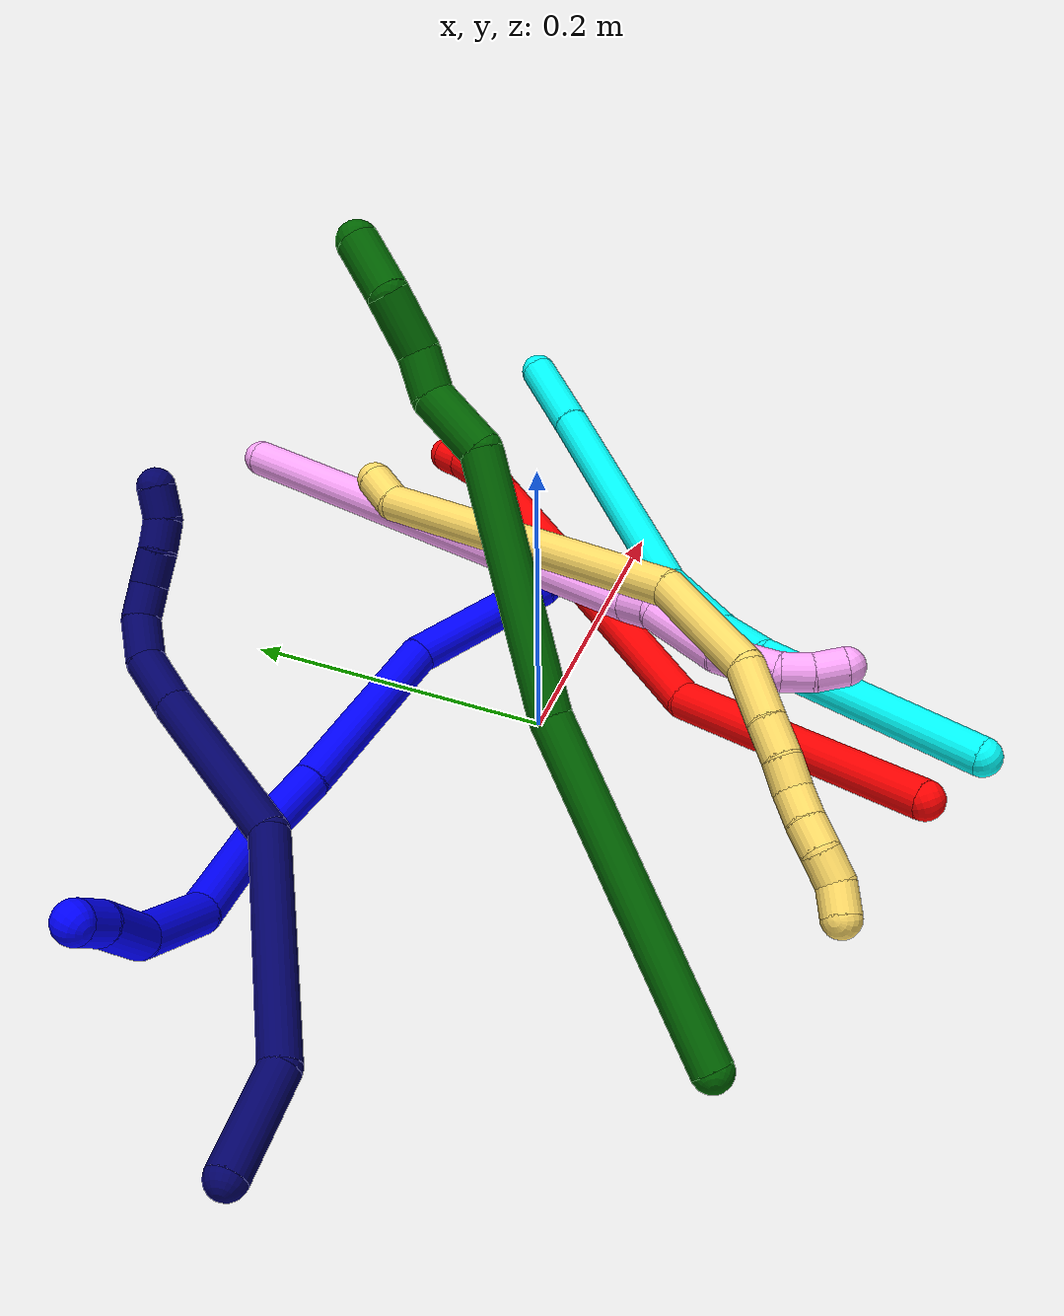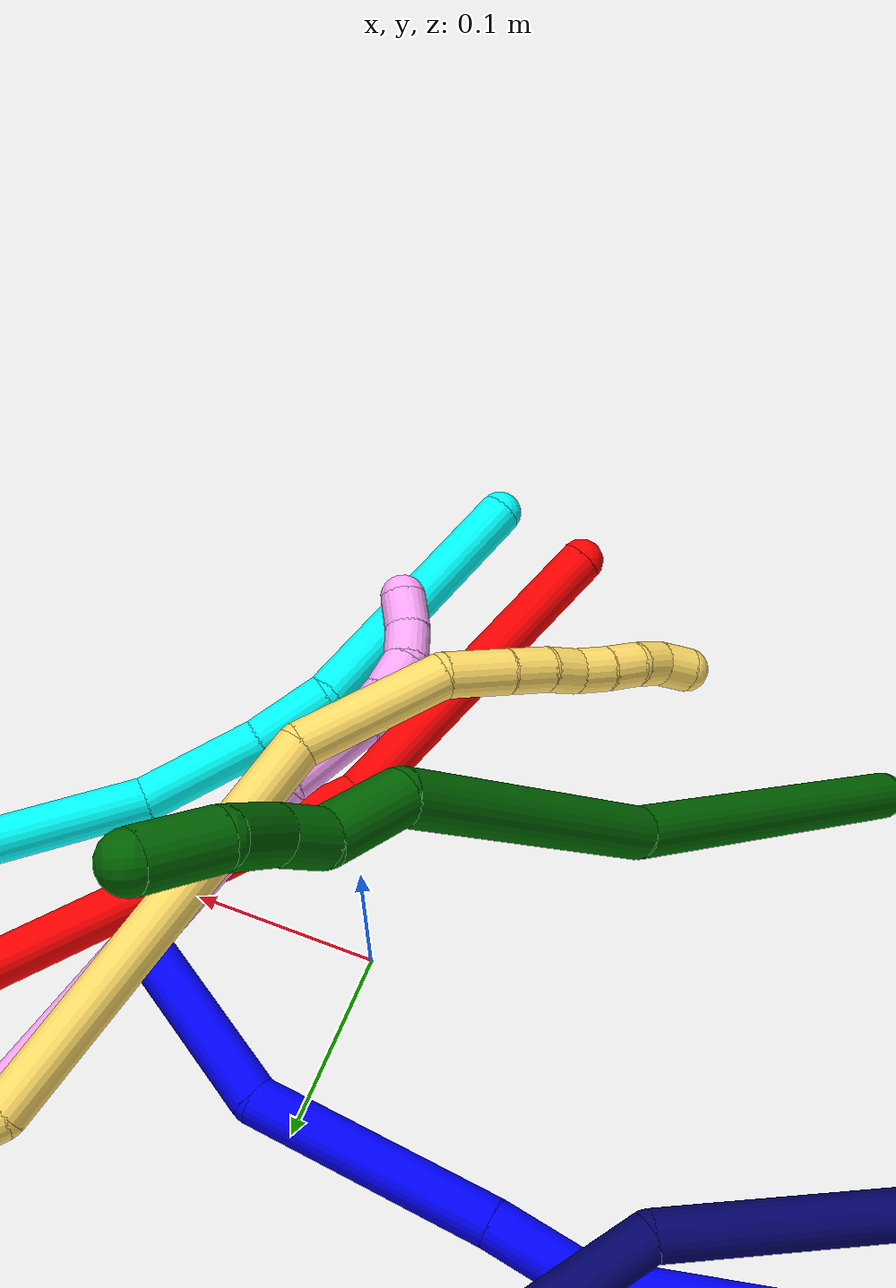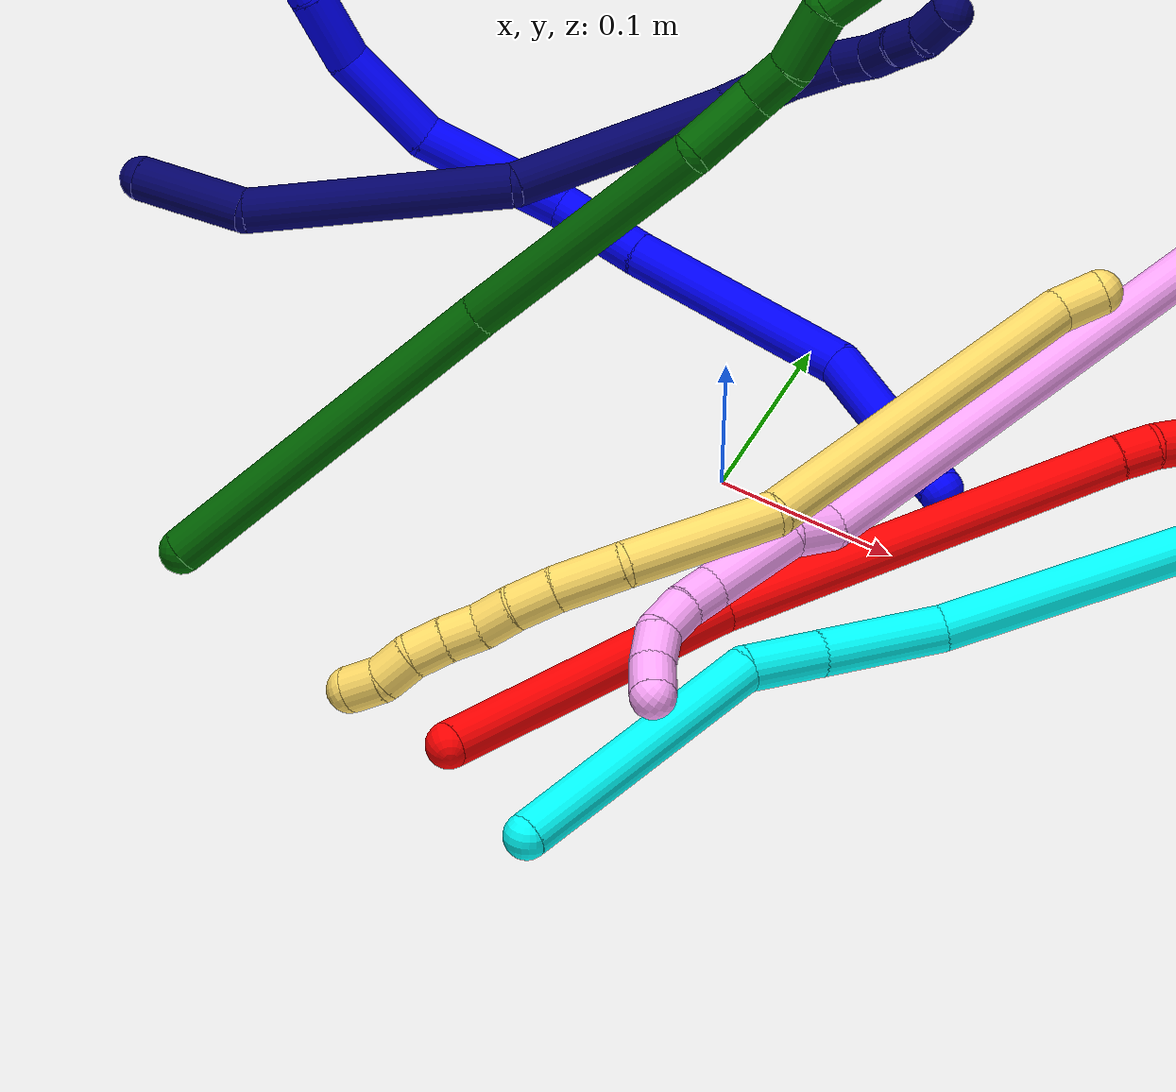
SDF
<sdf version="1.7">
 <world name="default">
  <plugin name="TubeGeneratorPlugin" filename="libtube_generator_plugin.so"/>
  <model name="photoneo_s_sensor">
   <static>1</static>
   <pose>0 0 2 1.57079 1.57079 3.14159</pose>
   <link name="link">
    <inertial><mass>0.1</mass></inertial>
    <sensor name="sensor" type="depth">
     <update_rate>30</update_rate>
     <camera>
      <horizontal_fov>1.22</horizontal_fov>
      <image><width>1920</width><height>1200</height><format>B8G8R8</format></image>
      <clip><near>0.1</near><far>4</far></clip>
      <depth_camera><output>points</output></depth_camera>
     </camera>
     <plugin name="camera_plugin" filename="libgazebo_ros_depth_camera.so">
      <baseline>0.2</baseline>
      <alwaysOn>1</alwaysOn>
      <updateRate>0.0</updateRate>
      <cameraName>camera_ir</cameraName>
      <imageTopicName>/camera/color/image_raw</imageTopicName>
      <cameraInfoTopicName>/camera/color/camera_info</cameraInfoTopicName>
      <depthImageTopicName>/camera/depth/image_raw</depthImageTopicName>
      <depthImageCameraInfoTopicName>/camera/depth/camera_info</depthImageCameraInfoTopicName>
      <pointCloudTopicName>/camera/depth/points</pointCloudTopicName>
      <frameName>fr_optical</frameName>
      <pointCloudCutoff>0.1</pointCloudCutoff>
      <pointCloudCutoffMax>2.0</pointCloudCutoffMax>
      <distortionK1>0</distortionK1>
      <distortionK2>0</distortionK2>
      <distortionK3>0</distortionK3>
      <distortionT1>0</distortionT1>
      <distortionT2>0</distortionT2>
      <CxPrime>0</CxPrime>
      <Cx>0</Cx>
      <Cy>0</Cy>
      <focalLength>0</focalLength>
      <hackBaseline>0</hackBaseline>
     </plugin>
    </sensor>
   </link>
  </model>
  <gravity>0 0 -9.8</gravity>
  <magnetic_field>6e-06 2.3e-05 -4.2e-05</magnetic_field>
  <atmosphere type="adiabatic"/>
  <physics name="default_physics" default="0" type="ode">
   <max_step_size>0.003</max_step_size>
   <real_time_factor>1</real_time_factor>
   <real_time_update_rate>1000</real_time_update_rate>
   <max_contacts>10000</max_contacts>
   <ode>
    <solver>
     <type>quick</type>
     <iters>100</iters>
     <sor>1.3</sor>
     <use_dynamic_moi_rescaling>0</use_dynamic_moi_rescaling>
    </solver>
    <constraints>
     <contact_max_correcting_vel>0</contact_max_correcting_vel>
     <contact_surface_layer>0.001</contact_surface_layer>
     <cfm>0</cfm>
     <erp>0.2</erp>
    </constraints>
   </ode>
  </physics>
  <scene><ambient>0.4 0.4 0.4 1</ambient><background>0.7 0.7 0.7 1</background><shadows>0</shadows></scene>
  <audio><device>default</device></audio>
  <spherical_coordinates>
   <surface_model>EARTH_WGS84</surface_model>
   <latitude_deg>0</latitude_deg>
   <longitude_deg>0</longitude_deg>
   <elevation>0</elevation>
   <heading_deg>0</heading_deg>
  </spherical_coordinates>
  <model name="bin">
   <static>1</static>
   <link name="bottom">
    <collision name="collision-bottom">
     <pose>0 0 -0.01 0 -0 0</pose>
     <geometry><box><size>0.8 0.6 0.02</size></box></geometry>
     <surface>
      <friction><ode><mu>100</mu><mu2>100</mu2></ode></friction>
      <contact><collide_bitmask>65535</collide_bitmask></contact>
     </surface>
    </collision>
   </link>
   <link name="west_wall">
    <collision name="collision-west_wall">
     <pose>-0.41 0 0.1 0 -0 0</pose>
     <geometry><box><size>0.02 0.6 0.2</size></box></geometry>
     <surface>
      <friction><ode><mu>100</mu><mu2>100</mu2></ode></friction>
      <contact><collide_bitmask>65535</collide_bitmask></contact>
     </surface>
    </collision>
   </link>
   <link name="east_wall">
    <collision name="collision-east_wall">
     <pose>0.41 0 0.1 0 -0 0</pose>
     <geometry><box><size>0.02 0.6 0.2</size></box></geometry>
     <surface>
      <friction><ode><mu>100</mu><mu2>100</mu2></ode></friction>
      <contact><collide_bitmask>65535</collide_bitmask></contact>
     </surface>
    </collision>
   </link>
   <link name="south_wall">
    <collision name="collision-south_wall">
     <pose>0 -0.31 0.1 0 -0 0</pose>
     <geometry><box><size>0.8 0.02 0.2</size></box></geometry>
     <surface>
      <friction><ode><mu>100</mu><mu2>100</mu2></ode></friction>
      <contact><collide_bitmask>65535</collide_bitmask></contact>
     </surface>
    </collision>
   </link>
   <link name="north_wall">
    <collision name="collision-north_wall">
     <pose>0 0.31 0.1 0 -0 0</pose>
     <geometry><box><size>0.8 0.02 0.2</size></box></geometry>
     <surface>
      <friction><ode><mu>100</mu><mu2>100</mu2></ode></friction>
      <contact><collide_bitmask>65535</collide_bitmask></contact>
     </surface>
    </collision>
   </link>
  </model>
  <model name="1">
   <static>0</static>
   <link name="1">
    <collision name="collision-cylinder-e_1_1_4">
     <pose>-0.049438 0.010562 0.009803 -0.82267 -1.28717 0.632482</pose>
     <geometry><cylinder><radius>0.0125</radius><length>0.102991</length></cylinder></geometry>
     <surface>
      <friction><ode><mu>1.16</mu><mu2>1.16</mu2><slip1>0</slip1><slip2>0</slip2></ode></friction>
      <contact><ode><kp>1e+06</kp><kd>1</kd><max_vel>0</max_vel><min_depth>0.001</min_depth></ode></contact>
     </surface>
    </collision>
    <visual name="visual-cylinder-e_1_1_4">
     <pose>-0.049438 0.010562 0.009803 -0.82267 -1.28717 0.632482</pose>
     <geometry><cylinder><radius>0.0125</radius><length>0.102991</length></cylinder></geometry>
     <material><ambient>0 0 1 1</ambient></material>
    </visual>
    <collision name="collision-cylinder-e_2_4_5">
     <pose>-0.16135 0.0333 0.003315 -2.49978 -1.25607 2.28299</pose>
     <geometry><cylinder><radius>0.0125</radius><length>0.131402</length></cylinder></geometry>
     <surface>
      <friction><ode><mu>1.16</mu><mu2>1.16</mu2><slip1>0</slip1><slip2>0</slip2></ode></friction>
      <contact><ode><kp>1e+06</kp><kd>1</kd><max_vel>0</max_vel><min_depth>0.001</min_depth></ode></contact>
     </surface>
    </collision>
    <visual name="visual-cylinder-e_2_4_5">
     <pose>-0.16135 0.0333 0.003315 -2.49978 -1.25607 2.28299</pose>
     <geometry><cylinder><radius>0.0125</radius><length>0.131402</length></cylinder></geometry>
     <material><ambient>0 0 1 1</ambient></material>
    </visual>
    <collision name="collision-cylinder-e_3_5_6">
     <pose>-0.250029 0.050732 -0.0179 -2.32349 -1.30257 2.10738</pose>
     <geometry><cylinder><radius>0.0125</radius><length>0.054354</length></cylinder></geometry>
     <surface>
      <friction><ode><mu>1.16</mu><mu2>1.16</mu2><slip1>0</slip1><slip2>0</slip2></ode></friction>
      <contact><ode><kp>1e+06</kp><kd>1</kd><max_vel>0</max_vel><min_depth>0.001</min_depth></ode></contact>
     </surface>
    </collision>
    <visual name="visual-cylinder-e_3_5_6">
     <pose>-0.250029 0.050732 -0.0179 -2.32349 -1.30257 2.10738</pose>
     <geometry><cylinder><radius>0.0125</radius><length>0.054354</length></cylinder></geometry>
     <material><ambient>0 0 1 1</ambient></material>
    </visual>
    <collision name="collision-cylinder-e_4_6_7">
     <pose>-0.313489 0.052282 -0.04301 2.95998 -1.06726 -2.83575</pose>
     <geometry><cylinder><radius>0.0125</radius><length>0.085068</length></cylinder></geometry>
     <surface>
      <friction><ode><mu>1.16</mu><mu2>1.16</mu2><slip1>0</slip1><slip2>0</slip2></ode></friction>
      <contact><ode><kp>1e+06</kp><kd>1</kd><max_vel>0</max_vel><min_depth>0.001</min_depth></ode></contact>
     </surface>
    </collision>
    <visual name="visual-cylinder-e_4_6_7">
     <pose>-0.313489 0.052282 -0.04301 2.95998 -1.06726 -2.83575</pose>
     <geometry><cylinder><radius>0.0125</radius><length>0.085068</length></cylinder></geometry>
     <material><ambient>0 0 1 1</ambient></material>
    </visual>
    <collision name="collision-cylinder-e_5_7_8">
     <pose>-0.377193 0.03664 -0.072095 2.2115 -1.05814 -1.72314</pose>
     <geometry><cylinder><radius>0.0125</radius><length>0.060703</length></cylinder></geometry>
     <surface>
      <friction><ode><mu>1.16</mu><mu2>1.16</mu2><slip1>0</slip1><slip2>0</slip2></ode></friction>
      <contact><ode><kp>1e+06</kp><kd>1</kd><max_vel>0</max_vel><min_depth>0.001</min_depth></ode></contact>
     </surface>
    </collision>
    <visual name="visual-cylinder-e_5_7_8">
     <pose>-0.377193 0.03664 -0.072095 2.2115 -1.05814 -1.72314</pose>
     <geometry><cylinder><radius>0.0125</radius><length>0.060703</length></cylinder></geometry>
     <material><ambient>0 0 1 1</ambient></material>
    </visual>
    <collision name="collision-cylinder-e_6_8_9">
     <pose>-0.418264 0.009176 -0.085555 1.85645 -0.734673 -0.94967</pose>
     <geometry><cylinder><radius>0.0125</radius><length>0.043624</length></cylinder></geometry>
     <surface>
      <friction><ode><mu>1.16</mu><mu2>1.16</mu2><slip1>0</slip1><slip2>0</slip2></ode></friction>
      <contact><ode><kp>1e+06</kp><kd>1</kd><max_vel>0</max_vel><min_depth>0.001</min_depth></ode></contact>
     </surface>
    </collision>
    <visual name="visual-cylinder-e_6_8_9">
     <pose>-0.418264 0.009176 -0.085555 1.85645 -0.734673 -0.94967</pose>
     <geometry><cylinder><radius>0.0125</radius><length>0.043624</length></cylinder></geometry>
     <material><ambient>0 0 1 1</ambient></material>
    </visual>
    <collision name="collision-cylinder-e_7_9_2">
     <pose>-0.441523 -0.01276 -0.092065 1.86623 -0.911343 -1.16871</pose>
     <geometry><cylinder><radius>0.0125</radius><length>0.021859</length></cylinder></geometry>
     <surface>
      <friction><ode><mu>1.16</mu><mu2>1.16</mu2><slip1>0</slip1><slip2>0</slip2></ode></friction>
      <contact><ode><kp>1e+06</kp><kd>1</kd><max_vel>0</max_vel><min_depth>0.001</min_depth></ode></contact>
     </surface>
    </collision>
    <visual name="visual-cylinder-e_7_9_2">
     <pose>-0.441523 -0.01276 -0.092065 1.86623 -0.911343 -1.16871</pose>
     <geometry><cylinder><radius>0.0125</radius><length>0.021859</length></cylinder></geometry>
     <material><ambient>0 0 1 1</ambient></material>
    </visual>
    <collision name="collision-sphere-2">
     <pose>-0.450161 -0.019166 -0.094015 0 -0 0</pose>
     <geometry><sphere><radius>0.0125</radius></sphere></geometry>
     <surface>
      <friction><ode><mu>1.16</mu><mu2>1.16</mu2><slip1>0</slip1><slip2>0</slip2></ode></friction>
      <contact><ode><kp>1e+06</kp><kd>1</kd><max_vel>0</max_vel><min_depth>0.001</min_depth></ode></contact>
     </surface>
    </collision>
    <visual name="visual-sphere-2">
     <pose>-0.450161 -0.019166 -0.094015 0 -0 0</pose>
     <geometry><sphere><radius>0.0125</radius></sphere></geometry>
     <material><ambient>0 0 1 1</ambient></material>
    </visual>
    <collision name="collision-sphere-9">
     <pose>-0.432885 -0.006354 -0.090116 0 -0 0</pose>
     <geometry><sphere><radius>0.0125</radius></sphere></geometry>
     <surface>
      <friction><ode><mu>1.16</mu><mu2>1.16</mu2><slip1>0</slip1><slip2>0</slip2></ode></friction>
      <contact><ode><kp>1e+06</kp><kd>1</kd><max_vel>0</max_vel><min_depth>0.001</min_depth></ode></contact>
     </surface>
    </collision>
    <visual name="visual-sphere-9">
     <pose>-0.432885 -0.006354 -0.090116 0 -0 0</pose>
     <geometry><sphere><radius>0.0125</radius></sphere></geometry>
     <material><ambient>0 0 1 1</ambient></material>
    </visual>
    <collision name="collision-sphere-4">
     <pose>-0.098876 0.021124 0.019606 0 -0 0</pose>
     <geometry><sphere><radius>0.0125</radius></sphere></geometry>
     <surface>
      <friction><ode><mu>1.16</mu><mu2>1.16</mu2><slip1>0</slip1><slip2>0</slip2></ode></friction>
      <contact><ode><kp>1e+06</kp><kd>1</kd><max_vel>0</max_vel><min_depth>0.001</min_depth></ode></contact>
     </surface>
    </collision>
    <visual name="visual-sphere-4">
     <pose>-0.098876 0.021124 0.019606 0 -0 0</pose>
     <geometry><sphere><radius>0.0125</radius></sphere></geometry>
     <material><ambient>0 0 1 1</ambient></material>
    </visual>
    <collision name="collision-sphere-1">
     <geometry><sphere><radius>0.0125</radius></sphere></geometry>
     <surface>
      <friction><ode><mu>1.16</mu><mu2>1.16</mu2><slip1>0</slip1><slip2>0</slip2></ode></friction>
      <contact><ode><kp>1e+06</kp><kd>1</kd><max_vel>0</max_vel><min_depth>0.001</min_depth></ode></contact>
     </surface>
    </collision>
    <visual name="visual-sphere-1">
     <geometry><sphere><radius>0.0125</radius></sphere></geometry>
     <material><ambient>0 0 1 1</ambient></material>
    </visual>
    <collision name="collision-sphere-8">
     <pose>-0.403643 0.024705 -0.080994 0 -0 0</pose>
     <geometry><sphere><radius>0.0125</radius></sphere></geometry>
     <surface>
      <friction><ode><mu>1.16</mu><mu2>1.16</mu2><slip1>0</slip1><slip2>0</slip2></ode></friction>
      <contact><ode><kp>1e+06</kp><kd>1</kd><max_vel>0</max_vel><min_depth>0.001</min_depth></ode></contact>
     </surface>
    </collision>
    <visual name="visual-sphere-8">
     <pose>-0.403643 0.024705 -0.080994 0 -0 0</pose>
     <geometry><sphere><radius>0.0125</radius></sphere></geometry>
     <material><ambient>0 0 1 1</ambient></material>
    </visual>
    <collision name="collision-sphere-5">
     <pose>-0.223824 0.045475 -0.012976 0 -0 0</pose>
     <geometry><sphere><radius>0.0125</radius></sphere></geometry>
     <surface>
      <friction><ode><mu>1.16</mu><mu2>1.16</mu2><slip1>0</slip1><slip2>0</slip2></ode></friction>
      <contact><ode><kp>1e+06</kp><kd>1</kd><max_vel>0</max_vel><min_depth>0.001</min_depth></ode></contact>
     </surface>
    </collision>
    <visual name="visual-sphere-5">
     <pose>-0.223824 0.045475 -0.012976 0 -0 0</pose>
     <geometry><sphere><radius>0.0125</radius></sphere></geometry>
     <material><ambient>0 0 1 1</ambient></material>
    </visual>
    <collision name="collision-sphere-6">
     <pose>-0.276234 0.055989 -0.022824 0 -0 0</pose>
     <geometry><sphere><radius>0.0125</radius></sphere></geometry>
     <surface>
      <friction><ode><mu>1.16</mu><mu2>1.16</mu2><slip1>0</slip1><slip2>0</slip2></ode></friction>
      <contact><ode><kp>1e+06</kp><kd>1</kd><max_vel>0</max_vel><min_depth>0.001</min_depth></ode></contact>
     </surface>
    </collision>
    <visual name="visual-sphere-6">
     <pose>-0.276234 0.055989 -0.022824 0 -0 0</pose>
     <geometry><sphere><radius>0.0125</radius></sphere></geometry>
     <material><ambient>0 0 1 1</ambient></material>
    </visual>
    <collision name="collision-sphere-7">
     <pose>-0.350744 0.048575 -0.063196 0 -0 0</pose>
     <geometry><sphere><radius>0.0125</radius></sphere></geometry>
     <surface>
      <friction><ode><mu>1.16</mu><mu2>1.16</mu2><slip1>0</slip1><slip2>0</slip2></ode></friction>
      <contact><ode><kp>1e+06</kp><kd>1</kd><max_vel>0</max_vel><min_depth>0.001</min_depth></ode></contact>
     </surface>
    </collision>
    <visual name="visual-sphere-7">
     <pose>-0.350744 0.048575 -0.063196 0 -0 0</pose>
     <geometry><sphere><radius>0.0125</radius></sphere></geometry>
     <material><ambient>0 0 1 1</ambient></material>
    </visual>
    <inertial>
     <pose>-0.234691 0.030028 -0.026615 0 -0 0</pose>
     <mass>0.5</mass>
     <inertia>
      <ixx>-3.7e-05</ixx>
      <ixy>0</ixy>
      <ixz>0</ixz>
      <iyy>0.000405</iyy>
      <iyz>0</iyz>
      <izz>0.000319</izz>
     </inertia>
    </inertial>
   </link>
   <pose>0.109525 0.040349 0.016612 -1.66535 0.176938 -0.374094</pose>
  </model>
  <model name="2">
   <static>0</static>
   <link name="2">
    <collision name="collision-cylinder-e_1_1_4">
     <pose>0.029769 0.070137 0.052926 -0.924347 0.326663 -0.163825</pose>
     <geometry><cylinder><radius>0.0125</radius><length>0.185543</length></cylinder></geometry>
     <surface>
      <friction><ode><mu>1.16</mu><mu2>1.16</mu2><slip1>0</slip1><slip2>0</slip2></ode></friction>
      <contact><ode><kp>1e+06</kp><kd>1</kd><max_vel>0</max_vel><min_depth>0.001</min_depth></ode></contact>
     </surface>
    </collision>
    <visual name="visual-cylinder-e_1_1_4">
     <pose>0.029769 0.070137 0.052926 -0.924347 0.326663 -0.163825</pose>
     <geometry><cylinder><radius>0.0125</radius><length>0.185543</length></cylinder></geometry>
     <material><ambient>1 0 0 1</ambient></material>
    </visual>
    <collision name="collision-cylinder-e_2_4_5">
     <pose>0.124277 0.230007 0.137899 -1.22779 0.596791 -0.426917</pose>
     <geometry><cylinder><radius>0.0125</radius><length>0.230393</length></cylinder></geometry>
     <surface>
      <friction><ode><mu>1.16</mu><mu2>1.16</mu2><slip1>0</slip1><slip2>0</slip2></ode></friction>
      <contact><ode><kp>1e+06</kp><kd>1</kd><max_vel>0</max_vel><min_depth>0.001</min_depth></ode></contact>
     </surface>
    </collision>
    <visual name="visual-cylinder-e_2_4_5">
     <pose>0.124277 0.230007 0.137899 -1.22779 0.596791 -0.426917</pose>
     <geometry><cylinder><radius>0.0125</radius><length>0.230393</length></cylinder></geometry>
     <material><ambient>1 0 0 1</ambient></material>
    </visual>
    <collision name="collision-cylinder-e_3_5_6">
     <pose>0.194474 0.328233 0.172702 -1.25688 0.548622 -0.403446</pose>
     <geometry><cylinder><radius>0.0125</radius><length>0.020928</length></cylinder></geometry>
     <surface>
      <friction><ode><mu>1.16</mu><mu2>1.16</mu2><slip1>0</slip1><slip2>0</slip2></ode></friction>
      <contact><ode><kp>1e+06</kp><kd>1</kd><max_vel>0</max_vel><min_depth>0.001</min_depth></ode></contact>
     </surface>
    </collision>
    <visual name="visual-cylinder-e_3_5_6">
     <pose>0.194474 0.328233 0.172702 -1.25688 0.548622 -0.403446</pose>
     <geometry><cylinder><radius>0.0125</radius><length>0.020928</length></cylinder></geometry>
     <material><ambient>1 0 0 1</ambient></material>
    </visual>
    <collision name="collision-cylinder-e_4_6_7">
     <pose>0.205636 0.355736 0.182611 -1.21099 0.273804 -0.190154</pose>
     <geometry><cylinder><radius>0.0125</radius><length>0.042197</length></cylinder></geometry>
     <surface>
      <friction><ode><mu>1.16</mu><mu2>1.16</mu2><slip1>0</slip1><slip2>0</slip2></ode></friction>
      <contact><ode><kp>1e+06</kp><kd>1</kd><max_vel>0</max_vel><min_depth>0.001</min_depth></ode></contact>
     </surface>
    </collision>
    <visual name="visual-cylinder-e_4_6_7">
     <pose>0.205636 0.355736 0.182611 -1.21099 0.273804 -0.190154</pose>
     <geometry><cylinder><radius>0.0125</radius><length>0.042197</length></cylinder></geometry>
     <material><ambient>1 0 0 1</ambient></material>
    </visual>
    <collision name="collision-cylinder-e_5_7_2">
     <pose>0.214912 0.383137 0.194909 -1.02049 0.34807 -0.196168</pose>
     <geometry><cylinder><radius>0.0125</radius><length>0.020939</length></cylinder></geometry>
     <surface>
      <friction><ode><mu>1.16</mu><mu2>1.16</mu2><slip1>0</slip1><slip2>0</slip2></ode></friction>
      <contact><ode><kp>1e+06</kp><kd>1</kd><max_vel>0</max_vel><min_depth>0.001</min_depth></ode></contact>
     </surface>
    </collision>
    <visual name="visual-cylinder-e_5_7_2">
     <pose>0.214912 0.383137 0.194909 -1.02049 0.34807 -0.196168</pose>
     <geometry><cylinder><radius>0.0125</radius><length>0.020939</length></cylinder></geometry>
     <material><ambient>1 0 0 1</ambient></material>
    </visual>
    <collision name="collision-sphere-2">
     <pose>0.218483 0.391526 0.200056 0 -0 0</pose>
     <geometry><sphere><radius>0.0125</radius></sphere></geometry>
     <surface>
      <friction><ode><mu>1.16</mu><mu2>1.16</mu2><slip1>0</slip1><slip2>0</slip2></ode></friction>
      <contact><ode><kp>1e+06</kp><kd>1</kd><max_vel>0</max_vel><min_depth>0.001</min_depth></ode></contact>
     </surface>
    </collision>
    <visual name="visual-sphere-2">
     <pose>0.218483 0.391526 0.200056 0 -0 0</pose>
     <geometry><sphere><radius>0.0125</radius></sphere></geometry>
     <material><ambient>1 0 0 1</ambient></material>
    </visual>
    <collision name="collision-sphere-7">
     <pose>0.211341 0.374748 0.189763 0 -0 0</pose>
     <geometry><sphere><radius>0.0125</radius></sphere></geometry>
     <surface>
      <friction><ode><mu>1.16</mu><mu2>1.16</mu2><slip1>0</slip1><slip2>0</slip2></ode></friction>
      <contact><ode><kp>1e+06</kp><kd>1</kd><max_vel>0</max_vel><min_depth>0.001</min_depth></ode></contact>
     </surface>
    </collision>
    <visual name="visual-sphere-7">
     <pose>0.211341 0.374748 0.189763 0 -0 0</pose>
     <geometry><sphere><radius>0.0125</radius></sphere></geometry>
     <material><ambient>1 0 0 1</ambient></material>
    </visual>
    <collision name="collision-sphere-6">
     <pose>0.199931 0.336725 0.175459 0 -0 0</pose>
     <geometry><sphere><radius>0.0125</radius></sphere></geometry>
     <surface>
      <friction><ode><mu>1.16</mu><mu2>1.16</mu2><slip1>0</slip1><slip2>0</slip2></ode></friction>
      <contact><ode><kp>1e+06</kp><kd>1</kd><max_vel>0</max_vel><min_depth>0.001</min_depth></ode></contact>
     </surface>
    </collision>
    <visual name="visual-sphere-6">
     <pose>0.199931 0.336725 0.175459 0 -0 0</pose>
     <geometry><sphere><radius>0.0125</radius></sphere></geometry>
     <material><ambient>1 0 0 1</ambient></material>
    </visual>
    <collision name="collision-sphere-5">
     <pose>0.189017 0.31974 0.169945 0 -0 0</pose>
     <geometry><sphere><radius>0.0125</radius></sphere></geometry>
     <surface>
      <friction><ode><mu>1.16</mu><mu2>1.16</mu2><slip1>0</slip1><slip2>0</slip2></ode></friction>
      <contact><ode><kp>1e+06</kp><kd>1</kd><max_vel>0</max_vel><min_depth>0.001</min_depth></ode></contact>
     </surface>
    </collision>
    <visual name="visual-sphere-5">
     <pose>0.189017 0.31974 0.169945 0 -0 0</pose>
     <geometry><sphere><radius>0.0125</radius></sphere></geometry>
     <material><ambient>1 0 0 1</ambient></material>
    </visual>
    <collision name="collision-sphere-1">
     <geometry><sphere><radius>0.0125</radius></sphere></geometry>
     <surface>
      <friction><ode><mu>1.16</mu><mu2>1.16</mu2><slip1>0</slip1><slip2>0</slip2></ode></friction>
      <contact><ode><kp>1e+06</kp><kd>1</kd><max_vel>0</max_vel><min_depth>0.001</min_depth></ode></contact>
     </surface>
    </collision>
    <visual name="visual-sphere-1">
     <geometry><sphere><radius>0.0125</radius></sphere></geometry>
     <material><ambient>1 0 0 1</ambient></material>
    </visual>
    <collision name="collision-sphere-4">
     <pose>0.059538 0.140274 0.105853 0 -0 0</pose>
     <geometry><sphere><radius>0.0125</radius></sphere></geometry>
     <surface>
      <friction><ode><mu>1.16</mu><mu2>1.16</mu2><slip1>0</slip1><slip2>0</slip2></ode></friction>
      <contact><ode><kp>1e+06</kp><kd>1</kd><max_vel>0</max_vel><min_depth>0.001</min_depth></ode></contact>
     </surface>
    </collision>
    <visual name="visual-sphere-4">
     <pose>0.059538 0.140274 0.105853 0 -0 0</pose>
     <geometry><sphere><radius>0.0125</radius></sphere></geometry>
     <material><ambient>1 0 0 1</ambient></material>
    </visual>
    <inertial>
     <pose>0.102806 0.191816 0.113984 0 -0 0</pose>
     <mass>0.5</mass>
     <inertia>
      <ixx>0.000868</ixx>
      <ixy>0</ixy>
      <ixz>0</ixz>
      <iyy>0.000481</iyy>
      <iyz>0</iyz>
      <izz>-0.001957</izz>
     </inertia>
    </inertial>
   </link>
   <pose>-0.0254 -0.25074 0.049345 -2.05779 -1.03241 1.02697</pose>
  </model>
  <model name="3">
   <static>0</static>
   <link name="3">
    <collision name="collision-cylinder-e_1_1_4">
     <pose>0.021519 0.072475 0.020413 -1.29625 0.278378 -0.211383</pose>
     <geometry><cylinder><radius>0.0125</radius><length>0.156618</length></cylinder></geometry>
     <surface>
      <friction><ode><mu>1.16</mu><mu2>1.16</mu2><slip1>0</slip1><slip2>0</slip2></ode></friction>
      <contact><ode><kp>1e+06</kp><kd>1</kd><max_vel>0</max_vel><min_depth>0.001</min_depth></ode></contact>
     </surface>
    </collision>
    <visual name="visual-cylinder-e_1_1_4">
     <pose>0.021519 0.072475 0.020413 -1.29625 0.278378 -0.211383</pose>
     <geometry><cylinder><radius>0.0125</radius><length>0.156618</length></cylinder></geometry>
     <material><ambient>0.003922 1 0.996078 1</ambient></material>
    </visual>
    <collision name="collision-cylinder-e_2_4_5">
     <pose>0.055112 0.163714 0.040282 -1.59979 0.57154 -0.587416</pose>
     <geometry><cylinder><radius>0.0125</radius><length>0.04464</length></cylinder></geometry>
     <surface>
      <friction><ode><mu>1.16</mu><mu2>1.16</mu2><slip1>0</slip1><slip2>0</slip2></ode></friction>
      <contact><ode><kp>1e+06</kp><kd>1</kd><max_vel>0</max_vel><min_depth>0.001</min_depth></ode></contact>
     </surface>
    </collision>
    <visual name="visual-cylinder-e_2_4_5">
     <pose>0.055112 0.163714 0.040282 -1.59979 0.57154 -0.587416</pose>
     <geometry><cylinder><radius>0.0125</radius><length>0.04464</length></cylinder></geometry>
     <material><ambient>0.003922 1 0.996078 1</ambient></material>
    </visual>
    <collision name="collision-cylinder-e_3_5_6">
     <pose>0.089049 0.209823 0.041684 -1.49975 0.673253 -0.63014</pose>
     <geometry><cylinder><radius>0.0125</radius><length>0.070129</length></cylinder></geometry>
     <surface>
      <friction><ode><mu>1.16</mu><mu2>1.16</mu2><slip1>0</slip1><slip2>0</slip2></ode></friction>
      <contact><ode><kp>1e+06</kp><kd>1</kd><max_vel>0</max_vel><min_depth>0.001</min_depth></ode></contact>
     </surface>
    </collision>
    <visual name="visual-cylinder-e_3_5_6">
     <pose>0.089049 0.209823 0.041684 -1.49975 0.673253 -0.63014</pose>
     <geometry><cylinder><radius>0.0125</radius><length>0.070129</length></cylinder></geometry>
     <material><ambient>0.003922 1 0.996078 1</ambient></material>
    </visual>
    <collision name="collision-cylinder-e_4_6_7">
     <pose>0.170368 0.290165 0.070022 -1.10876 0.787493 -0.503526</pose>
     <geometry><cylinder><radius>0.0125</radius><length>0.167812</length></cylinder></geometry>
     <surface>
      <friction><ode><mu>1.16</mu><mu2>1.16</mu2><slip1>0</slip1><slip2>0</slip2></ode></friction>
      <contact><ode><kp>1e+06</kp><kd>1</kd><max_vel>0</max_vel><min_depth>0.001</min_depth></ode></contact>
     </surface>
    </collision>
    <visual name="visual-cylinder-e_4_6_7">
     <pose>0.170368 0.290165 0.070022 -1.10876 0.787493 -0.503526</pose>
     <geometry><cylinder><radius>0.0125</radius><length>0.167812</length></cylinder></geometry>
     <material><ambient>0.003922 1 0.996078 1</ambient></material>
    </visual>
    <collision name="collision-cylinder-e_5_7_2">
     <pose>0.25139 0.362719 0.105165 -1.15004 0.788743 -0.526885</pose>
     <geometry><cylinder><radius>0.0125</radius><length>0.060801</length></cylinder></geometry>
     <surface>
      <friction><ode><mu>1.16</mu><mu2>1.16</mu2><slip1>0</slip1><slip2>0</slip2></ode></friction>
      <contact><ode><kp>1e+06</kp><kd>1</kd><max_vel>0</max_vel><min_depth>0.001</min_depth></ode></contact>
     </surface>
    </collision>
    <visual name="visual-cylinder-e_5_7_2">
     <pose>0.25139 0.362719 0.105165 -1.15004 0.788743 -0.526885</pose>
     <geometry><cylinder><radius>0.0125</radius><length>0.060801</length></cylinder></geometry>
     <material><ambient>0.003922 1 0.996078 1</ambient></material>
    </visual>
    <collision name="collision-sphere-2">
     <pose>0.272958 0.382275 0.113916 0 -0 0</pose>
     <geometry><sphere><radius>0.0125</radius></sphere></geometry>
     <surface>
      <friction><ode><mu>1.16</mu><mu2>1.16</mu2><slip1>0</slip1><slip2>0</slip2></ode></friction>
      <contact><ode><kp>1e+06</kp><kd>1</kd><max_vel>0</max_vel><min_depth>0.001</min_depth></ode></contact>
     </surface>
    </collision>
    <visual name="visual-sphere-2">
     <pose>0.272958 0.382275 0.113916 0 -0 0</pose>
     <geometry><sphere><radius>0.0125</radius></sphere></geometry>
     <material><ambient>0.003922 1 0.996078 1</ambient></material>
    </visual>
    <collision name="collision-sphere-7">
     <pose>0.229822 0.343164 0.096414 0 -0 0</pose>
     <geometry><sphere><radius>0.0125</radius></sphere></geometry>
     <surface>
      <friction><ode><mu>1.16</mu><mu2>1.16</mu2><slip1>0</slip1><slip2>0</slip2></ode></friction>
      <contact><ode><kp>1e+06</kp><kd>1</kd><max_vel>0</max_vel><min_depth>0.001</min_depth></ode></contact>
     </surface>
    </collision>
    <visual name="visual-sphere-7">
     <pose>0.229822 0.343164 0.096414 0 -0 0</pose>
     <geometry><sphere><radius>0.0125</radius></sphere></geometry>
     <material><ambient>0.003922 1 0.996078 1</ambient></material>
    </visual>
    <collision name="collision-sphere-6">
     <pose>0.110913 0.237167 0.04363 0 -0 0</pose>
     <geometry><sphere><radius>0.0125</radius></sphere></geometry>
     <surface>
      <friction><ode><mu>1.16</mu><mu2>1.16</mu2><slip1>0</slip1><slip2>0</slip2></ode></friction>
      <contact><ode><kp>1e+06</kp><kd>1</kd><max_vel>0</max_vel><min_depth>0.001</min_depth></ode></contact>
     </surface>
    </collision>
    <visual name="visual-sphere-6">
     <pose>0.110913 0.237167 0.04363 0 -0 0</pose>
     <geometry><sphere><radius>0.0125</radius></sphere></geometry>
     <material><ambient>0.003922 1 0.996078 1</ambient></material>
    </visual>
    <collision name="collision-sphere-5">
     <pose>0.067185 0.182479 0.039738 0 -0 0</pose>
     <geometry><sphere><radius>0.0125</radius></sphere></geometry>
     <surface>
      <friction><ode><mu>1.16</mu><mu2>1.16</mu2><slip1>0</slip1><slip2>0</slip2></ode></friction>
      <contact><ode><kp>1e+06</kp><kd>1</kd><max_vel>0</max_vel><min_depth>0.001</min_depth></ode></contact>
     </surface>
    </collision>
    <visual name="visual-sphere-5">
     <pose>0.067185 0.182479 0.039738 0 -0 0</pose>
     <geometry><sphere><radius>0.0125</radius></sphere></geometry>
     <material><ambient>0.003922 1 0.996078 1</ambient></material>
    </visual>
    <collision name="collision-sphere-1">
     <geometry><sphere><radius>0.0125</radius></sphere></geometry>
     <surface>
      <friction><ode><mu>1.16</mu><mu2>1.16</mu2><slip1>0</slip1><slip2>0</slip2></ode></friction>
      <contact><ode><kp>1e+06</kp><kd>1</kd><max_vel>0</max_vel><min_depth>0.001</min_depth></ode></contact>
     </surface>
    </collision>
    <visual name="visual-sphere-1">
     <geometry><sphere><radius>0.0125</radius></sphere></geometry>
     <material><ambient>0.003922 1 0.996078 1</ambient></material>
    </visual>
    <collision name="collision-sphere-4">
     <pose>0.043038 0.144949 0.040826 0 -0 0</pose>
     <geometry><sphere><radius>0.0125</radius></sphere></geometry>
     <surface>
      <friction><ode><mu>1.16</mu><mu2>1.16</mu2><slip1>0</slip1><slip2>0</slip2></ode></friction>
      <contact><ode><kp>1e+06</kp><kd>1</kd><max_vel>0</max_vel><min_depth>0.001</min_depth></ode></contact>
     </surface>
    </collision>
    <visual name="visual-sphere-4">
     <pose>0.043038 0.144949 0.040826 0 -0 0</pose>
     <geometry><sphere><radius>0.0125</radius></sphere></geometry>
     <material><ambient>0.003922 1 0.996078 1</ambient></material>
    </visual>
    <inertial>
     <pose>0.1119 0.208241 0.052126 0 -0 0</pose>
     <mass>0.5</mass>
     <inertia>
      <ixx>0.000386</ixx>
      <ixy>0</ixy>
      <ixz>0</ixz>
      <iyy>0.000215</iyy>
      <iyz>0</iyz>
      <izz>-0.001005</izz>
     </inertia>
    </inertial>
   </link>
   <pose>0.033082 -0.274042 0.038686 -0.352175 -0.123339 -0.008142</pose>
  </model>
  <model name="4">
   <static>0</static>
   <link name="4">
    <collision name="collision-cylinder-e_1_1_4">
     <pose>-0.038864 -0.127163 -0.101561 2.24472 -0.234419 -0.480037</pose>
     <geometry><cylinder><radius>0.0125</radius><length>0.334637</length></cylinder></geometry>
     <surface>
      <friction><ode><mu>1.16</mu><mu2>1.16</mu2><slip1>0</slip1><slip2>0</slip2></ode></friction>
      <contact><ode><kp>1e+06</kp><kd>1</kd><max_vel>0</max_vel><min_depth>0.001</min_depth></ode></contact>
     </surface>
    </collision>
    <visual name="visual-cylinder-e_1_1_4">
     <pose>-0.038864 -0.127163 -0.101561 2.24472 -0.234419 -0.480037</pose>
     <geometry><cylinder><radius>0.0125</radius><length>0.334637</length></cylinder></geometry>
     <material><ambient>1 0.65098 0.996078 1</ambient></material>
    </visual>
    <collision name="collision-cylinder-e_2_4_5">
     <pose>-0.085096 -0.264943 -0.208273 2.02253 -0.558133 -0.858184</pose>
     <geometry><cylinder><radius>0.0125</radius><length>0.027821</length></cylinder></geometry>
     <surface>
      <friction><ode><mu>1.16</mu><mu2>1.16</mu2><slip1>0</slip1><slip2>0</slip2></ode></friction>
      <contact><ode><kp>1e+06</kp><kd>1</kd><max_vel>0</max_vel><min_depth>0.001</min_depth></ode></contact>
     </surface>
    </collision>
    <visual name="visual-cylinder-e_2_4_5">
     <pose>-0.085096 -0.264943 -0.208273 2.02253 -0.558133 -0.858184</pose>
     <geometry><cylinder><radius>0.0125</radius><length>0.027821</length></cylinder></geometry>
     <material><ambient>1 0.65098 0.996078 1</ambient></material>
    </visual>
    <collision name="collision-cylinder-e_3_5_6">
     <pose>-0.099659 -0.291801 -0.232637 2.43981 -0.278569 -0.731526</pose>
     <geometry><cylinder><radius>0.0125</radius><length>0.052336</length></cylinder></geometry>
     <surface>
      <friction><ode><mu>1.16</mu><mu2>1.16</mu2><slip1>0</slip1><slip2>0</slip2></ode></friction>
      <contact><ode><kp>1e+06</kp><kd>1</kd><max_vel>0</max_vel><min_depth>0.001</min_depth></ode></contact>
     </surface>
    </collision>
    <visual name="visual-cylinder-e_3_5_6">
     <pose>-0.099659 -0.291801 -0.232637 2.43981 -0.278569 -0.731526</pose>
     <geometry><cylinder><radius>0.0125</radius><length>0.052336</length></cylinder></geometry>
     <material><ambient>1 0.65098 0.996078 1</ambient></material>
    </visual>
    <collision name="collision-cylinder-e_4_6_7">
     <pose>-0.109534 -0.316693 -0.257805 2.17369 -0.249861 -0.46904</pose>
     <geometry><cylinder><radius>0.0125</radius><length>0.021675</length></cylinder></geometry>
     <surface>
      <friction><ode><mu>1.16</mu><mu2>1.16</mu2><slip1>0</slip1><slip2>0</slip2></ode></friction>
      <contact><ode><kp>1e+06</kp><kd>1</kd><max_vel>0</max_vel><min_depth>0.001</min_depth></ode></contact>
     </surface>
    </collision>
    <visual name="visual-cylinder-e_4_6_7">
     <pose>-0.109534 -0.316693 -0.257805 2.17369 -0.249861 -0.46904</pose>
     <geometry><cylinder><radius>0.0125</radius><length>0.021675</length></cylinder></geometry>
     <material><ambient>1 0.65098 0.996078 1</ambient></material>
    </visual>
    <collision name="collision-cylinder-e_5_7_8">
     <pose>-0.113043 -0.334224 -0.270131 2.19305 -0.075668 -0.147203</pose>
     <geometry><cylinder><radius>0.0125</radius><length>0.021925</length></cylinder></geometry>
     <surface>
      <friction><ode><mu>1.16</mu><mu2>1.16</mu2><slip1>0</slip1><slip2>0</slip2></ode></friction>
      <contact><ode><kp>1e+06</kp><kd>1</kd><max_vel>0</max_vel><min_depth>0.001</min_depth></ode></contact>
     </surface>
    </collision>
    <visual name="visual-cylinder-e_5_7_8">
     <pose>-0.113043 -0.334224 -0.270131 2.19305 -0.075668 -0.147203</pose>
     <geometry><cylinder><radius>0.0125</radius><length>0.021925</length></cylinder></geometry>
     <material><ambient>1 0.65098 0.996078 1</ambient></material>
    </visual>
    <collision name="collision-cylinder-e_6_8_9">
     <pose>-0.110022 -0.351492 -0.281283 2.08894 0.379474 0.638489</pose>
     <geometry><cylinder><radius>0.0125</radius><length>0.020784</length></cylinder></geometry>
     <surface>
      <friction><ode><mu>1.16</mu><mu2>1.16</mu2><slip1>0</slip1><slip2>0</slip2></ode></friction>
      <contact><ode><kp>1e+06</kp><kd>1</kd><max_vel>0</max_vel><min_depth>0.001</min_depth></ode></contact>
     </surface>
    </collision>
    <visual name="visual-cylinder-e_6_8_9">
     <pose>-0.110022 -0.351492 -0.281283 2.08894 0.379474 0.638489</pose>
     <geometry><cylinder><radius>0.0125</radius><length>0.020784</length></cylinder></geometry>
     <material><ambient>1 0.65098 0.996078 1</ambient></material>
    </visual>
    <collision name="collision-cylinder-e_7_9_2">
     <pose>-0.101381 -0.368707 -0.288799 1.87122 0.478268 0.638865</pose>
     <geometry><cylinder><radius>0.0125</radius><length>0.020822</length></cylinder></geometry>
     <surface>
      <friction><ode><mu>1.16</mu><mu2>1.16</mu2><slip1>0</slip1><slip2>0</slip2></ode></friction>
      <contact><ode><kp>1e+06</kp><kd>1</kd><max_vel>0</max_vel><min_depth>0.001</min_depth></ode></contact>
     </surface>
    </collision>
    <visual name="visual-cylinder-e_7_9_2">
     <pose>-0.101381 -0.368707 -0.288799 1.87122 0.478268 0.638865</pose>
     <geometry><cylinder><radius>0.0125</radius><length>0.020822</length></cylinder></geometry>
     <material><ambient>1 0.65098 0.996078 1</ambient></material>
    </visual>
    <collision name="collision-sphere-2">
     <pose>-0.096589 -0.377536 -0.291534 0 -0 0</pose>
     <geometry><sphere><radius>0.0125</radius></sphere></geometry>
     <surface>
      <friction><ode><mu>1.16</mu><mu2>1.16</mu2><slip1>0</slip1><slip2>0</slip2></ode></friction>
      <contact><ode><kp>1e+06</kp><kd>1</kd><max_vel>0</max_vel><min_depth>0.001</min_depth></ode></contact>
     </surface>
    </collision>
    <visual name="visual-sphere-2">
     <pose>-0.096589 -0.377536 -0.291534 0 -0 0</pose>
     <geometry><sphere><radius>0.0125</radius></sphere></geometry>
     <material><ambient>1 0.65098 0.996078 1</ambient></material>
    </visual>
    <collision name="collision-sphere-9">
     <pose>-0.106172 -0.359878 -0.286064 0 -0 0</pose>
     <geometry><sphere><radius>0.0125</radius></sphere></geometry>
     <surface>
      <friction><ode><mu>1.16</mu><mu2>1.16</mu2><slip1>0</slip1><slip2>0</slip2></ode></friction>
      <contact><ode><kp>1e+06</kp><kd>1</kd><max_vel>0</max_vel><min_depth>0.001</min_depth></ode></contact>
     </surface>
    </collision>
    <visual name="visual-sphere-9">
     <pose>-0.106172 -0.359878 -0.286064 0 -0 0</pose>
     <geometry><sphere><radius>0.0125</radius></sphere></geometry>
     <material><ambient>1 0.65098 0.996078 1</ambient></material>
    </visual>
    <collision name="collision-sphere-4">
     <pose>-0.077729 -0.254326 -0.203122 0 -0 0</pose>
     <geometry><sphere><radius>0.0125</radius></sphere></geometry>
     <surface>
      <friction><ode><mu>1.16</mu><mu2>1.16</mu2><slip1>0</slip1><slip2>0</slip2></ode></friction>
      <contact><ode><kp>1e+06</kp><kd>1</kd><max_vel>0</max_vel><min_depth>0.001</min_depth></ode></contact>
     </surface>
    </collision>
    <visual name="visual-sphere-4">
     <pose>-0.077729 -0.254326 -0.203122 0 -0 0</pose>
     <geometry><sphere><radius>0.0125</radius></sphere></geometry>
     <material><ambient>1 0.65098 0.996078 1</ambient></material>
    </visual>
    <collision name="collision-sphere-1">
     <geometry><sphere><radius>0.0125</radius></sphere></geometry>
     <surface>
      <friction><ode><mu>1.16</mu><mu2>1.16</mu2><slip1>0</slip1><slip2>0</slip2></ode></friction>
      <contact><ode><kp>1e+06</kp><kd>1</kd><max_vel>0</max_vel><min_depth>0.001</min_depth></ode></contact>
     </surface>
    </collision>
    <visual name="visual-sphere-1">
     <geometry><sphere><radius>0.0125</radius></sphere></geometry>
     <material><ambient>1 0.65098 0.996078 1</ambient></material>
    </visual>
    <collision name="collision-sphere-8">
     <pose>-0.113871 -0.343106 -0.276502 0 -0 0</pose>
     <geometry><sphere><radius>0.0125</radius></sphere></geometry>
     <surface>
      <friction><ode><mu>1.16</mu><mu2>1.16</mu2><slip1>0</slip1><slip2>0</slip2></ode></friction>
      <contact><ode><kp>1e+06</kp><kd>1</kd><max_vel>0</max_vel><min_depth>0.001</min_depth></ode></contact>
     </surface>
    </collision>
    <visual name="visual-sphere-8">
     <pose>-0.113871 -0.343106 -0.276502 0 -0 0</pose>
     <geometry><sphere><radius>0.0125</radius></sphere></geometry>
     <material><ambient>1 0.65098 0.996078 1</ambient></material>
    </visual>
    <collision name="collision-sphere-5">
     <pose>-0.092463 -0.275559 -0.213423 0 -0 0</pose>
     <geometry><sphere><radius>0.0125</radius></sphere></geometry>
     <surface>
      <friction><ode><mu>1.16</mu><mu2>1.16</mu2><slip1>0</slip1><slip2>0</slip2></ode></friction>
      <contact><ode><kp>1e+06</kp><kd>1</kd><max_vel>0</max_vel><min_depth>0.001</min_depth></ode></contact>
     </surface>
    </collision>
    <visual name="visual-sphere-5">
     <pose>-0.092463 -0.275559 -0.213423 0 -0 0</pose>
     <geometry><sphere><radius>0.0125</radius></sphere></geometry>
     <material><ambient>1 0.65098 0.996078 1</ambient></material>
    </visual>
    <collision name="collision-sphere-6">
     <pose>-0.106854 -0.308043 -0.251851 0 -0 0</pose>
     <geometry><sphere><radius>0.0125</radius></sphere></geometry>
     <surface>
      <friction><ode><mu>1.16</mu><mu2>1.16</mu2><slip1>0</slip1><slip2>0</slip2></ode></friction>
      <contact><ode><kp>1e+06</kp><kd>1</kd><max_vel>0</max_vel><min_depth>0.001</min_depth></ode></contact>
     </surface>
    </collision>
    <visual name="visual-sphere-6">
     <pose>-0.106854 -0.308043 -0.251851 0 -0 0</pose>
     <geometry><sphere><radius>0.0125</radius></sphere></geometry>
     <material><ambient>1 0.65098 0.996078 1</ambient></material>
    </visual>
    <collision name="collision-sphere-7">
     <pose>-0.112214 -0.325342 -0.26376 0 -0 0</pose>
     <geometry><sphere><radius>0.0125</radius></sphere></geometry>
     <surface>
      <friction><ode><mu>1.16</mu><mu2>1.16</mu2><slip1>0</slip1><slip2>0</slip2></ode></friction>
      <contact><ode><kp>1e+06</kp><kd>1</kd><max_vel>0</max_vel><min_depth>0.001</min_depth></ode></contact>
     </surface>
    </collision>
    <visual name="visual-sphere-7">
     <pose>-0.112214 -0.325342 -0.26376 0 -0 0</pose>
     <geometry><sphere><radius>0.0125</radius></sphere></geometry>
     <material><ambient>1 0.65098 0.996078 1</ambient></material>
    </visual>
    <inertial>
     <pose>-0.059678 -0.188742 -0.150651 0 -0 0</pose>
     <mass>0.5</mass>
     <inertia>
      <ixx>0.001296</ixx>
      <ixy>0</ixy>
      <ixz>0</ixz>
      <iyy>-0.002929</iyy>
      <iyz>0</iyz>
      <izz>0.00311</izz>
     </inertia>
    </inertial>
   </link>
   <pose>0.173917 0.288306 0.016196 -0.677335 0.404573 -0.070796</pose>
  </model>
  <model name="5">
   <static>0</static>
   <link name="5">
    <collision name="collision-cylinder-e_1_1_4">
     <pose>-0.008416 -0.009524 0.003096 1.25649 -0.698874 -0.517537</pose>
     <geometry><cylinder><radius>0.0125</radius><length>0.026163</length></cylinder></geometry>
     <surface>
      <friction><ode><mu>1.16</mu><mu2>1.16</mu2><slip1>0</slip1><slip2>0</slip2></ode></friction>
      <contact><ode><kp>1e+06</kp><kd>1</kd><max_vel>0</max_vel><min_depth>0.001</min_depth></ode></contact>
     </surface>
    </collision>
    <visual name="visual-cylinder-e_1_1_4">
     <pose>-0.008416 -0.009524 0.003096 1.25649 -0.698874 -0.517537</pose>
     <geometry><cylinder><radius>0.0125</radius><length>0.026163</length></cylinder></geometry>
     <material><ambient>1 0.858824 0.4 1</ambient></material>
    </visual>
    <collision name="collision-cylinder-e_2_4_5">
     <pose>-0.048258 -0.127487 0.017082 1.47071 -0.280743 -0.254266</pose>
     <geometry><cylinder><radius>0.0125</radius><length>0.22685</length></cylinder></geometry>
     <surface>
      <friction><ode><mu>1.16</mu><mu2>1.16</mu2><slip1>0</slip1><slip2>0</slip2></ode></friction>
      <contact><ode><kp>1e+06</kp><kd>1</kd><max_vel>0</max_vel><min_depth>0.001</min_depth></ode></contact>
     </surface>
    </collision>
    <visual name="visual-cylinder-e_2_4_5">
     <pose>-0.048258 -0.127487 0.017082 1.47071 -0.280743 -0.254266</pose>
     <geometry><cylinder><radius>0.0125</radius><length>0.22685</length></cylinder></geometry>
     <material><ambient>1 0.858824 0.4 1</ambient></material>
    </visual>
    <collision name="collision-cylinder-e_3_5_6">
     <pose>-0.104012 -0.267489 0.041625 1.16251 -0.61566 -0.411824</pose>
     <geometry><cylinder><radius>0.0125</radius><length>0.084249</length></cylinder></geometry>
     <surface>
      <friction><ode><mu>1.16</mu><mu2>1.16</mu2><slip1>0</slip1><slip2>0</slip2></ode></friction>
      <contact><ode><kp>1e+06</kp><kd>1</kd><max_vel>0</max_vel><min_depth>0.001</min_depth></ode></contact>
     </surface>
    </collision>
    <visual name="visual-cylinder-e_3_5_6">
     <pose>-0.104012 -0.267489 0.041625 1.16251 -0.61566 -0.411824</pose>
     <geometry><cylinder><radius>0.0125</radius><length>0.084249</length></cylinder></geometry>
     <material><ambient>1 0.858824 0.4 1</ambient></material>
    </visual>
    <collision name="collision-cylinder-e_4_6_7">
     <pose>-0.144462 -0.307814 0.060131 1.06503 -1.01496 -0.633318</pose>
     <geometry><cylinder><radius>0.0125</radius><length>0.037961</length></cylinder></geometry>
     <surface>
      <friction><ode><mu>1.16</mu><mu2>1.16</mu2><slip1>0</slip1><slip2>0</slip2></ode></friction>
      <contact><ode><kp>1e+06</kp><kd>1</kd><max_vel>0</max_vel><min_depth>0.001</min_depth></ode></contact>
     </surface>
    </collision>
    <visual name="visual-cylinder-e_4_6_7">
     <pose>-0.144462 -0.307814 0.060131 1.06503 -1.01496 -0.633318</pose>
     <geometry><cylinder><radius>0.0125</radius><length>0.037961</length></cylinder></geometry>
     <material><ambient>1 0.858824 0.4 1</ambient></material>
    </visual>
    <collision name="collision-cylinder-e_5_7_8">
     <pose>-0.171294 -0.322213 0.067155 1.20312 -1.05707 -0.762462</pose>
     <geometry><cylinder><radius>0.0125</radius><length>0.02459</length></cylinder></geometry>
     <surface>
      <friction><ode><mu>1.16</mu><mu2>1.16</mu2><slip1>0</slip1><slip2>0</slip2></ode></friction>
      <contact><ode><kp>1e+06</kp><kd>1</kd><max_vel>0</max_vel><min_depth>0.001</min_depth></ode></contact>
     </surface>
    </collision>
    <visual name="visual-cylinder-e_5_7_8">
     <pose>-0.171294 -0.322213 0.067155 1.20312 -1.05707 -0.762462</pose>
     <geometry><cylinder><radius>0.0125</radius><length>0.02459</length></cylinder></geometry>
     <material><ambient>1 0.858824 0.4 1</ambient></material>
    </visual>
    <collision name="collision-cylinder-e_6_8_9">
     <pose>-0.191357 -0.331573 0.069995 1.39325 -1.18674 -1.02736</pose>
     <geometry><cylinder><radius>0.0125</radius><length>0.020181</length></cylinder></geometry>
     <surface>
      <friction><ode><mu>1.16</mu><mu2>1.16</mu2><slip1>0</slip1><slip2>0</slip2></ode></friction>
      <contact><ode><kp>1e+06</kp><kd>1</kd><max_vel>0</max_vel><min_depth>0.001</min_depth></ode></contact>
     </surface>
    </collision>
    <visual name="visual-cylinder-e_6_8_9">
     <pose>-0.191357 -0.331573 0.069995 1.39325 -1.18674 -1.02736</pose>
     <geometry><cylinder><radius>0.0125</radius><length>0.020181</length></cylinder></geometry>
     <material><ambient>1 0.858824 0.4 1</ambient></material>
    </visual>
    <collision name="collision-cylinder-e_7_9_10">
     <pose>-0.209195 -0.340028 0.07305 1.10366 -1.01213 -0.657594</pose>
     <geometry><cylinder><radius>0.0125</radius><length>0.020005</length></cylinder></geometry>
     <surface>
      <friction><ode><mu>1.16</mu><mu2>1.16</mu2><slip1>0</slip1><slip2>0</slip2></ode></friction>
      <contact><ode><kp>1e+06</kp><kd>1</kd><max_vel>0</max_vel><min_depth>0.001</min_depth></ode></contact>
     </surface>
    </collision>
    <visual name="visual-cylinder-e_7_9_10">
     <pose>-0.209195 -0.340028 0.07305 1.10366 -1.01213 -0.657594</pose>
     <geometry><cylinder><radius>0.0125</radius><length>0.020005</length></cylinder></geometry>
     <material><ambient>1 0.858824 0.4 1</ambient></material>
    </visual>
    <collision name="collision-cylinder-e_8_10_11">
     <pose>-0.226025 -0.350015 0.077083 1.26738 -0.987906 -0.753525</pose>
     <geometry><cylinder><radius>0.0125</radius><length>0.020001</length></cylinder></geometry>
     <surface>
      <friction><ode><mu>1.16</mu><mu2>1.16</mu2><slip1>0</slip1><slip2>0</slip2></ode></friction>
      <contact><ode><kp>1e+06</kp><kd>1</kd><max_vel>0</max_vel><min_depth>0.001</min_depth></ode></contact>
     </surface>
    </collision>
    <visual name="visual-cylinder-e_8_10_11">
     <pose>-0.226025 -0.350015 0.077083 1.26738 -0.987906 -0.753525</pose>
     <geometry><cylinder><radius>0.0125</radius><length>0.020001</length></cylinder></geometry>
     <material><ambient>1 0.858824 0.4 1</ambient></material>
    </visual>
    <collision name="collision-cylinder-e_9_11_12">
     <pose>-0.24333 -0.359652 0.077963 1.7434 -1.1096 -1.27042</pose>
     <geometry><cylinder><radius>0.0125</radius><length>0.02</length></cylinder></geometry>
     <surface>
      <friction><ode><mu>1.16</mu><mu2>1.16</mu2><slip1>0</slip1><slip2>0</slip2></ode></friction>
      <contact><ode><kp>1e+06</kp><kd>1</kd><max_vel>0</max_vel><min_depth>0.001</min_depth></ode></contact>
     </surface>
    </collision>
    <visual name="visual-cylinder-e_9_11_12">
     <pose>-0.24333 -0.359652 0.077963 1.7434 -1.1096 -1.27042</pose>
     <geometry><cylinder><radius>0.0125</radius><length>0.02</length></cylinder></geometry>
     <material><ambient>1 0.858824 0.4 1</ambient></material>
    </visual>
    <collision name="collision-cylinder-e_10_12_2">
     <pose>-0.261735 -0.366438 0.079419 0.824603 -1.23754 -0.603824</pose>
     <geometry><cylinder><radius>0.0125</radius><length>0.02</length></cylinder></geometry>
     <surface>
      <friction><ode><mu>1.16</mu><mu2>1.16</mu2><slip1>0</slip1><slip2>0</slip2></ode></friction>
      <contact><ode><kp>1e+06</kp><kd>1</kd><max_vel>0</max_vel><min_depth>0.001</min_depth></ode></contact>
     </surface>
    </collision>
    <visual name="visual-cylinder-e_10_12_2">
     <pose>-0.261735 -0.366438 0.079419 0.824603 -1.23754 -0.603824</pose>
     <geometry><cylinder><radius>0.0125</radius><length>0.02</length></cylinder></geometry>
     <material><ambient>1 0.858824 0.4 1</ambient></material>
    </visual>
    <collision name="collision-sphere-2">
     <pose>-0.271184 -0.36884 0.08164 0 -0 0</pose>
     <geometry><sphere><radius>0.0125</radius></sphere></geometry>
     <surface>
      <friction><ode><mu>1.16</mu><mu2>1.16</mu2><slip1>0</slip1><slip2>0</slip2></ode></friction>
      <contact><ode><kp>1e+06</kp><kd>1</kd><max_vel>0</max_vel><min_depth>0.001</min_depth></ode></contact>
     </surface>
    </collision>
    <visual name="visual-sphere-2">
     <pose>-0.271184 -0.36884 0.08164 0 -0 0</pose>
     <geometry><sphere><radius>0.0125</radius></sphere></geometry>
     <material><ambient>1 0.858824 0.4 1</ambient></material>
    </visual>
    <collision name="collision-sphere-12">
     <pose>-0.252285 -0.364037 0.077199 0 -0 0</pose>
     <geometry><sphere><radius>0.0125</radius></sphere></geometry>
     <surface>
      <friction><ode><mu>1.16</mu><mu2>1.16</mu2><slip1>0</slip1><slip2>0</slip2></ode></friction>
      <contact><ode><kp>1e+06</kp><kd>1</kd><max_vel>0</max_vel><min_depth>0.001</min_depth></ode></contact>
     </surface>
    </collision>
    <visual name="visual-sphere-12">
     <pose>-0.252285 -0.364037 0.077199 0 -0 0</pose>
     <geometry><sphere><radius>0.0125</radius></sphere></geometry>
     <material><ambient>1 0.858824 0.4 1</ambient></material>
    </visual>
    <collision name="collision-sphere-11">
     <pose>-0.234374 -0.355268 0.078727 0 -0 0</pose>
     <geometry><sphere><radius>0.0125</radius></sphere></geometry>
     <surface>
      <friction><ode><mu>1.16</mu><mu2>1.16</mu2><slip1>0</slip1><slip2>0</slip2></ode></friction>
      <contact><ode><kp>1e+06</kp><kd>1</kd><max_vel>0</max_vel><min_depth>0.001</min_depth></ode></contact>
     </surface>
    </collision>
    <visual name="visual-sphere-11">
     <pose>-0.234374 -0.355268 0.078727 0 -0 0</pose>
     <geometry><sphere><radius>0.0125</radius></sphere></geometry>
     <material><ambient>1 0.858824 0.4 1</ambient></material>
    </visual>
    <collision name="collision-sphere-10">
     <pose>-0.217676 -0.344762 0.075438 0 -0 0</pose>
     <geometry><sphere><radius>0.0125</radius></sphere></geometry>
     <surface>
      <friction><ode><mu>1.16</mu><mu2>1.16</mu2><slip1>0</slip1><slip2>0</slip2></ode></friction>
      <contact><ode><kp>1e+06</kp><kd>1</kd><max_vel>0</max_vel><min_depth>0.001</min_depth></ode></contact>
     </surface>
    </collision>
    <visual name="visual-sphere-10">
     <pose>-0.217676 -0.344762 0.075438 0 -0 0</pose>
     <geometry><sphere><radius>0.0125</radius></sphere></geometry>
     <material><ambient>1 0.858824 0.4 1</ambient></material>
    </visual>
    <collision name="collision-sphere-9">
     <pose>-0.200713 -0.335294 0.070663 0 -0 0</pose>
     <geometry><sphere><radius>0.0125</radius></sphere></geometry>
     <surface>
      <friction><ode><mu>1.16</mu><mu2>1.16</mu2><slip1>0</slip1><slip2>0</slip2></ode></friction>
      <contact><ode><kp>1e+06</kp><kd>1</kd><max_vel>0</max_vel><min_depth>0.001</min_depth></ode></contact>
     </surface>
    </collision>
    <visual name="visual-sphere-9">
     <pose>-0.200713 -0.335294 0.070663 0 -0 0</pose>
     <geometry><sphere><radius>0.0125</radius></sphere></geometry>
     <material><ambient>1 0.858824 0.4 1</ambient></material>
    </visual>
    <collision name="collision-sphere-4">
     <pose>-0.016832 -0.019048 0.006192 0 -0 0</pose>
     <geometry><sphere><radius>0.0125</radius></sphere></geometry>
     <surface>
      <friction><ode><mu>1.16</mu><mu2>1.16</mu2><slip1>0</slip1><slip2>0</slip2></ode></friction>
      <contact><ode><kp>1e+06</kp><kd>1</kd><max_vel>0</max_vel><min_depth>0.001</min_depth></ode></contact>
     </surface>
    </collision>
    <visual name="visual-sphere-4">
     <pose>-0.016832 -0.019048 0.006192 0 -0 0</pose>
     <geometry><sphere><radius>0.0125</radius></sphere></geometry>
     <material><ambient>1 0.858824 0.4 1</ambient></material>
    </visual>
    <collision name="collision-sphere-1">
     <geometry><sphere><radius>0.0125</radius></sphere></geometry>
     <surface>
      <friction><ode><mu>1.16</mu><mu2>1.16</mu2><slip1>0</slip1><slip2>0</slip2></ode></friction>
      <contact><ode><kp>1e+06</kp><kd>1</kd><max_vel>0</max_vel><min_depth>0.001</min_depth></ode></contact>
     </surface>
    </collision>
    <visual name="visual-sphere-1">
     <geometry><sphere><radius>0.0125</radius></sphere></geometry>
     <material><ambient>1 0.858824 0.4 1</ambient></material>
    </visual>
    <collision name="collision-sphere-8">
     <pose>-0.182002 -0.327852 0.069327 0 -0 0</pose>
     <geometry><sphere><radius>0.0125</radius></sphere></geometry>
     <surface>
      <friction><ode><mu>1.16</mu><mu2>1.16</mu2><slip1>0</slip1><slip2>0</slip2></ode></friction>
      <contact><ode><kp>1e+06</kp><kd>1</kd><max_vel>0</max_vel><min_depth>0.001</min_depth></ode></contact>
     </surface>
    </collision>
    <visual name="visual-sphere-8">
     <pose>-0.182002 -0.327852 0.069327 0 -0 0</pose>
     <geometry><sphere><radius>0.0125</radius></sphere></geometry>
     <material><ambient>1 0.858824 0.4 1</ambient></material>
    </visual>
    <collision name="collision-sphere-5">
     <pose>-0.079685 -0.235926 0.027971 0 -0 0</pose>
     <geometry><sphere><radius>0.0125</radius></sphere></geometry>
     <surface>
      <friction><ode><mu>1.16</mu><mu2>1.16</mu2><slip1>0</slip1><slip2>0</slip2></ode></friction>
      <contact><ode><kp>1e+06</kp><kd>1</kd><max_vel>0</max_vel><min_depth>0.001</min_depth></ode></contact>
     </surface>
    </collision>
    <visual name="visual-sphere-5">
     <pose>-0.079685 -0.235926 0.027971 0 -0 0</pose>
     <geometry><sphere><radius>0.0125</radius></sphere></geometry>
     <material><ambient>1 0.858824 0.4 1</ambient></material>
    </visual>
    <collision name="collision-sphere-6">
     <pose>-0.128339 -0.299052 0.055279 0 -0 0</pose>
     <geometry><sphere><radius>0.0125</radius></sphere></geometry>
     <surface>
      <friction><ode><mu>1.16</mu><mu2>1.16</mu2><slip1>0</slip1><slip2>0</slip2></ode></friction>
      <contact><ode><kp>1e+06</kp><kd>1</kd><max_vel>0</max_vel><min_depth>0.001</min_depth></ode></contact>
     </surface>
    </collision>
    <visual name="visual-sphere-6">
     <pose>-0.128339 -0.299052 0.055279 0 -0 0</pose>
     <geometry><sphere><radius>0.0125</radius></sphere></geometry>
     <material><ambient>1 0.858824 0.4 1</ambient></material>
    </visual>
    <collision name="collision-sphere-7">
     <pose>-0.160585 -0.316575 0.064984 0 -0 0</pose>
     <geometry><sphere><radius>0.0125</radius></sphere></geometry>
     <surface>
      <friction><ode><mu>1.16</mu><mu2>1.16</mu2><slip1>0</slip1><slip2>0</slip2></ode></friction>
      <contact><ode><kp>1e+06</kp><kd>1</kd><max_vel>0</max_vel><min_depth>0.001</min_depth></ode></contact>
     </surface>
    </collision>
    <visual name="visual-sphere-7">
     <pose>-0.160585 -0.316575 0.064984 0 -0 0</pose>
     <geometry><sphere><radius>0.0125</radius></sphere></geometry>
     <material><ambient>1 0.858824 0.4 1</ambient></material>
    </visual>
    <inertial>
     <pose>-0.104591 -0.21266 0.03792 0 -0 0</pose>
     <mass>0.5</mass>
     <inertia>
      <ixx>0.000678</ixx>
      <ixy>0</ixy>
      <ixz>0</ixz>
      <iyy>-8.1e-05</iyy>
      <iyz>0</iyz>
      <izz>0.001311</izz>
     </inertia>
    </inertial>
   </link>
   <pose>0.135023 0.17505 0.053459 -0.481668 -0.836542 0.365301</pose>
  </model>
  <model name="6">
   <static>0</static>
   <link name="6">
    <collision name="collision-cylinder-e_1_1_4">
     <pose>0.048731 0.051702 -0.075732 -2.54257 0.488474 -1.35803</pose>
     <geometry><cylinder><radius>0.0125</radius><length>0.207684</length></cylinder></geometry>
     <surface>
      <friction><ode><mu>1.16</mu><mu2>1.16</mu2><slip1>0</slip1><slip2>0</slip2></ode></friction>
      <contact><ode><kp>1e+06</kp><kd>1</kd><max_vel>0</max_vel><min_depth>0.001</min_depth></ode></contact>
     </surface>
    </collision>
    <visual name="visual-cylinder-e_1_1_4">
     <pose>0.048731 0.051702 -0.075732 -2.54257 0.488474 -1.35803</pose>
     <geometry><cylinder><radius>0.0125</radius><length>0.207684</length></cylinder></geometry>
     <material><ambient>0 0.392157 0.003922 1</ambient></material>
    </visual>
    <collision name="collision-cylinder-e_2_4_5">
     <pose>0.14391 0.131356 -0.204411 -2.65586 0.659809 -1.88887</pose>
     <geometry><cylinder><radius>0.0125</radius><length>0.151554</length></cylinder></geometry>
     <surface>
      <friction><ode><mu>1.16</mu><mu2>1.16</mu2><slip1>0</slip1><slip2>0</slip2></ode></friction>
      <contact><ode><kp>1e+06</kp><kd>1</kd><max_vel>0</max_vel><min_depth>0.001</min_depth></ode></contact>
     </surface>
    </collision>
    <visual name="visual-cylinder-e_2_4_5">
     <pose>0.14391 0.131356 -0.204411 -2.65586 0.659809 -1.88887</pose>
     <geometry><cylinder><radius>0.0125</radius><length>0.151554</length></cylinder></geometry>
     <material><ambient>0 0.392157 0.003922 1</ambient></material>
    </visual>
    <collision name="collision-cylinder-e_3_5_6">
     <pose>0.194911 0.173535 -0.272393 -2.38383 0.216456 -0.532859</pose>
     <geometry><cylinder><radius>0.0125</radius><length>0.042388</length></cylinder></geometry>
     <surface>
      <friction><ode><mu>1.16</mu><mu2>1.16</mu2><slip1>0</slip1><slip2>0</slip2></ode></friction>
      <contact><ode><kp>1e+06</kp><kd>1</kd><max_vel>0</max_vel><min_depth>0.001</min_depth></ode></contact>
     </surface>
    </collision>
    <visual name="visual-cylinder-e_3_5_6">
     <pose>0.194911 0.173535 -0.272393 -2.38383 0.216456 -0.532859</pose>
     <geometry><cylinder><radius>0.0125</radius><length>0.042388</length></cylinder></geometry>
     <material><ambient>0 0.392157 0.003922 1</ambient></material>
    </visual>
    <collision name="collision-cylinder-e_4_6_7">
     <pose>0.207418 0.193204 -0.296098 -2.581 0.660653 -1.7448</pose>
     <geometry><cylinder><radius>0.0125</radius><length>0.025927</length></cylinder></geometry>
     <surface>
      <friction><ode><mu>1.16</mu><mu2>1.16</mu2><slip1>0</slip1><slip2>0</slip2></ode></friction>
      <contact><ode><kp>1e+06</kp><kd>1</kd><max_vel>0</max_vel><min_depth>0.001</min_depth></ode></contact>
     </surface>
    </collision>
    <visual name="visual-cylinder-e_4_6_7">
     <pose>0.207418 0.193204 -0.296098 -2.581 0.660653 -1.7448</pose>
     <geometry><cylinder><radius>0.0125</radius><length>0.025927</length></cylinder></geometry>
     <material><ambient>0 0.392157 0.003922 1</ambient></material>
    </visual>
    <collision name="collision-cylinder-e_5_7_8">
     <pose>0.227239 0.209728 -0.312587 -2.18528 0.718762 -1.2545</pose>
     <geometry><cylinder><radius>0.0125</radius><length>0.036043</length></cylinder></geometry>
     <surface>
      <friction><ode><mu>1.16</mu><mu2>1.16</mu2><slip1>0</slip1><slip2>0</slip2></ode></friction>
      <contact><ode><kp>1e+06</kp><kd>1</kd><max_vel>0</max_vel><min_depth>0.001</min_depth></ode></contact>
     </surface>
    </collision>
    <visual name="visual-cylinder-e_5_7_8">
     <pose>0.227239 0.209728 -0.312587 -2.18528 0.718762 -1.2545</pose>
     <geometry><cylinder><radius>0.0125</radius><length>0.036043</length></cylinder></geometry>
     <material><ambient>0 0.392157 0.003922 1</ambient></material>
    </visual>
    <collision name="collision-cylinder-e_6_8_2">
     <pose>0.245043 0.230335 -0.334737 -2.55499 0.332293 -1.01374</pose>
     <geometry><cylinder><radius>0.0125</radius><length>0.036404</length></cylinder></geometry>
     <surface>
      <friction><ode><mu>1.16</mu><mu2>1.16</mu2><slip1>0</slip1><slip2>0</slip2></ode></friction>
      <contact><ode><kp>1e+06</kp><kd>1</kd><max_vel>0</max_vel><min_depth>0.001</min_depth></ode></contact>
     </surface>
    </collision>
    <visual name="visual-cylinder-e_6_8_2">
     <pose>0.245043 0.230335 -0.334737 -2.55499 0.332293 -1.01374</pose>
     <geometry><cylinder><radius>0.0125</radius><length>0.036404</length></cylinder></geometry>
     <material><ambient>0 0.392157 0.003922 1</ambient></material>
    </visual>
    <collision name="collision-sphere-2">
     <pose>0.25098 0.239859 -0.349067 0 -0 0</pose>
     <geometry><sphere><radius>0.0125</radius></sphere></geometry>
     <surface>
      <friction><ode><mu>1.16</mu><mu2>1.16</mu2><slip1>0</slip1><slip2>0</slip2></ode></friction>
      <contact><ode><kp>1e+06</kp><kd>1</kd><max_vel>0</max_vel><min_depth>0.001</min_depth></ode></contact>
     </surface>
    </collision>
    <visual name="visual-sphere-2">
     <pose>0.25098 0.239859 -0.349067 0 -0 0</pose>
     <geometry><sphere><radius>0.0125</radius></sphere></geometry>
     <material><ambient>0 0.392157 0.003922 1</ambient></material>
    </visual>
    <collision name="collision-sphere-4">
     <pose>0.097461 0.103404 -0.151464 0 -0 0</pose>
     <geometry><sphere><radius>0.0125</radius></sphere></geometry>
     <surface>
      <friction><ode><mu>1.16</mu><mu2>1.16</mu2><slip1>0</slip1><slip2>0</slip2></ode></friction>
      <contact><ode><kp>1e+06</kp><kd>1</kd><max_vel>0</max_vel><min_depth>0.001</min_depth></ode></contact>
     </surface>
    </collision>
    <visual name="visual-sphere-4">
     <pose>0.097461 0.103404 -0.151464 0 -0 0</pose>
     <geometry><sphere><radius>0.0125</radius></sphere></geometry>
     <material><ambient>0 0.392157 0.003922 1</ambient></material>
    </visual>
    <collision name="collision-sphere-1">
     <geometry><sphere><radius>0.0125</radius></sphere></geometry>
     <surface>
      <friction><ode><mu>1.16</mu><mu2>1.16</mu2><slip1>0</slip1><slip2>0</slip2></ode></friction>
      <contact><ode><kp>1e+06</kp><kd>1</kd><max_vel>0</max_vel><min_depth>0.001</min_depth></ode></contact>
     </surface>
    </collision>
    <visual name="visual-sphere-1">
     <geometry><sphere><radius>0.0125</radius></sphere></geometry>
     <material><ambient>0 0.392157 0.003922 1</ambient></material>
    </visual>
    <collision name="collision-sphere-8">
     <pose>0.239105 0.22081 -0.320407 0 -0 0</pose>
     <geometry><sphere><radius>0.0125</radius></sphere></geometry>
     <surface>
      <friction><ode><mu>1.16</mu><mu2>1.16</mu2><slip1>0</slip1><slip2>0</slip2></ode></friction>
      <contact><ode><kp>1e+06</kp><kd>1</kd><max_vel>0</max_vel><min_depth>0.001</min_depth></ode></contact>
     </surface>
    </collision>
    <visual name="visual-sphere-8">
     <pose>0.239105 0.22081 -0.320407 0 -0 0</pose>
     <geometry><sphere><radius>0.0125</radius></sphere></geometry>
     <material><ambient>0 0.392157 0.003922 1</ambient></material>
    </visual>
    <collision name="collision-sphere-5">
     <pose>0.190359 0.159308 -0.257358 0 -0 0</pose>
     <geometry><sphere><radius>0.0125</radius></sphere></geometry>
     <surface>
      <friction><ode><mu>1.16</mu><mu2>1.16</mu2><slip1>0</slip1><slip2>0</slip2></ode></friction>
      <contact><ode><kp>1e+06</kp><kd>1</kd><max_vel>0</max_vel><min_depth>0.001</min_depth></ode></contact>
     </surface>
    </collision>
    <visual name="visual-sphere-5">
     <pose>0.190359 0.159308 -0.257358 0 -0 0</pose>
     <geometry><sphere><radius>0.0125</radius></sphere></geometry>
     <material><ambient>0 0.392157 0.003922 1</ambient></material>
    </visual>
    <collision name="collision-sphere-6">
     <pose>0.199463 0.187762 -0.287429 0 -0 0</pose>
     <geometry><sphere><radius>0.0125</radius></sphere></geometry>
     <surface>
      <friction><ode><mu>1.16</mu><mu2>1.16</mu2><slip1>0</slip1><slip2>0</slip2></ode></friction>
      <contact><ode><kp>1e+06</kp><kd>1</kd><max_vel>0</max_vel><min_depth>0.001</min_depth></ode></contact>
     </surface>
    </collision>
    <visual name="visual-sphere-6">
     <pose>0.199463 0.187762 -0.287429 0 -0 0</pose>
     <geometry><sphere><radius>0.0125</radius></sphere></geometry>
     <material><ambient>0 0.392157 0.003922 1</ambient></material>
    </visual>
    <collision name="collision-sphere-7">
     <pose>0.215372 0.198646 -0.304767 0 -0 0</pose>
     <geometry><sphere><radius>0.0125</radius></sphere></geometry>
     <surface>
      <friction><ode><mu>1.16</mu><mu2>1.16</mu2><slip1>0</slip1><slip2>0</slip2></ode></friction>
      <contact><ode><kp>1e+06</kp><kd>1</kd><max_vel>0</max_vel><min_depth>0.001</min_depth></ode></contact>
     </surface>
    </collision>
    <visual name="visual-sphere-7">
     <pose>0.215372 0.198646 -0.304767 0 -0 0</pose>
     <geometry><sphere><radius>0.0125</radius></sphere></geometry>
     <material><ambient>0 0.392157 0.003922 1</ambient></material>
    </visual>
    <inertial>
     <pose>0.125363 0.117909 -0.178766 0 -0 0</pose>
     <mass>0.5</mass>
     <inertia>
      <ixx>-0.00079</ixx>
      <ixy>0</ixy>
      <ixz>0</ixz>
      <iyy>-0.000646</iyy>
      <iyz>0</iyz>
      <izz>-0.001069</izz>
     </inertia>
    </inertial>
   </link>
   <pose>-0.224178 -0.187051 0.011495 1.51785 -1.31288 -1.07895</pose>
  </model>
  <model name="7">
   <static>0</static>
   <link name="7">
    <collision name="collision-cylinder-e_1_1_4">
     <pose>-0.002018 -0.004856 -0.032349 2.99259 -0.061602 -0.78295</pose>
     <geometry><cylinder><radius>0.0125</radius><length>0.065547</length></cylinder></geometry>
     <surface>
      <friction><ode><mu>1.16</mu><mu2>1.16</mu2><slip1>0</slip1><slip2>0</slip2></ode></friction>
      <contact><ode><kp>1e+06</kp><kd>1</kd><max_vel>0</max_vel><min_depth>0.001</min_depth></ode></contact>
     </surface>
    </collision>
    <visual name="visual-cylinder-e_1_1_4">
     <pose>-0.002018 -0.004856 -0.032349 2.99259 -0.061602 -0.78295</pose>
     <geometry><cylinder><radius>0.0125</radius><length>0.065547</length></cylinder></geometry>
     <material><ambient>0.003922 0 0.403922 1</ambient></material>
    </visual>
    <collision name="collision-cylinder-e_2_4_5">
     <pose>0.018946 -0.000955 -0.135038 -3.01773 0.313521 -2.39382</pose>
     <geometry><cylinder><radius>0.0125</radius><length>0.149032</length></cylinder></geometry>
     <surface>
      <friction><ode><mu>1.16</mu><mu2>1.16</mu2><slip1>0</slip1><slip2>0</slip2></ode></friction>
      <contact><ode><kp>1e+06</kp><kd>1</kd><max_vel>0</max_vel><min_depth>0.001</min_depth></ode></contact>
     </surface>
    </collision>
    <visual name="visual-cylinder-e_2_4_5">
     <pose>0.018946 -0.000955 -0.135038 -3.01773 0.313521 -2.39382</pose>
     <geometry><cylinder><radius>0.0125</radius><length>0.149032</length></cylinder></geometry>
     <material><ambient>0.003922 0 0.403922 1</ambient></material>
    </visual>
    <collision name="collision-cylinder-e_3_5_6">
     <pose>0.074263 0.038481 -0.251085 -2.55045 0.531103 -1.4581</pose>
     <geometry><cylinder><radius>0.0125</radius><length>0.127683</length></cylinder></geometry>
     <surface>
      <friction><ode><mu>1.16</mu><mu2>1.16</mu2><slip1>0</slip1><slip2>0</slip2></ode></friction>
      <contact><ode><kp>1e+06</kp><kd>1</kd><max_vel>0</max_vel><min_depth>0.001</min_depth></ode></contact>
     </surface>
    </collision>
    <visual name="visual-cylinder-e_3_5_6">
     <pose>0.074263 0.038481 -0.251085 -2.55045 0.531103 -1.4581</pose>
     <geometry><cylinder><radius>0.0125</radius><length>0.127683</length></cylinder></geometry>
     <material><ambient>0.003922 0 0.403922 1</ambient></material>
    </visual>
    <collision name="collision-cylinder-e_4_6_7">
     <pose>0.11863 0.076564 -0.311592 -2.67774 0.628651 -1.88505</pose>
     <geometry><cylinder><radius>0.0125</radius><length>0.040924</length></cylinder></geometry>
     <surface>
      <friction><ode><mu>1.16</mu><mu2>1.16</mu2><slip1>0</slip1><slip2>0</slip2></ode></friction>
      <contact><ode><kp>1e+06</kp><kd>1</kd><max_vel>0</max_vel><min_depth>0.001</min_depth></ode></contact>
     </surface>
    </collision>
    <visual name="visual-cylinder-e_4_6_7">
     <pose>0.11863 0.076564 -0.311592 -2.67774 0.628651 -1.88505</pose>
     <geometry><cylinder><radius>0.0125</radius><length>0.040924</length></cylinder></geometry>
     <material><ambient>0.003922 0 0.403922 1</ambient></material>
    </visual>
    <collision name="collision-cylinder-e_5_7_8">
     <pose>0.137963 0.083824 -0.339473 3.13051 0.50902 3.09898</pose>
     <geometry><cylinder><radius>0.0125</radius><length>0.02996</length></cylinder></geometry>
     <surface>
      <friction><ode><mu>1.16</mu><mu2>1.16</mu2><slip1>0</slip1><slip2>0</slip2></ode></friction>
      <contact><ode><kp>1e+06</kp><kd>1</kd><max_vel>0</max_vel><min_depth>0.001</min_depth></ode></contact>
     </surface>
    </collision>
    <visual name="visual-cylinder-e_5_7_8">
     <pose>0.137963 0.083824 -0.339473 3.13051 0.50902 3.09898</pose>
     <geometry><cylinder><radius>0.0125</radius><length>0.02996</length></cylinder></geometry>
     <material><ambient>0.003922 0 0.403922 1</ambient></material>
    </visual>
    <collision name="collision-cylinder-e_6_8_9">
     <pose>0.149022 0.078785 -0.362207 2.67239 0.33429 1.22939</pose>
     <geometry><cylinder><radius>0.0125</radius><length>0.022916</length></cylinder></geometry>
     <surface>
      <friction><ode><mu>1.16</mu><mu2>1.16</mu2><slip1>0</slip1><slip2>0</slip2></ode></friction>
      <contact><ode><kp>1e+06</kp><kd>1</kd><max_vel>0</max_vel><min_depth>0.001</min_depth></ode></contact>
     </surface>
    </collision>
    <visual name="visual-cylinder-e_6_8_9">
     <pose>0.149022 0.078785 -0.362207 2.67239 0.33429 1.22939</pose>
     <geometry><cylinder><radius>0.0125</radius><length>0.022916</length></cylinder></geometry>
     <material><ambient>0.003922 0 0.403922 1</ambient></material>
    </visual>
    <collision name="collision-cylinder-e_7_9_10">
     <pose>0.156971 0.066461 -0.3793 2.3568 0.379227 0.868428</pose>
     <geometry><cylinder><radius>0.0125</radius><length>0.022634</length></cylinder></geometry>
     <surface>
      <friction><ode><mu>1.16</mu><mu2>1.16</mu2><slip1>0</slip1><slip2>0</slip2></ode></friction>
      <contact><ode><kp>1e+06</kp><kd>1</kd><max_vel>0</max_vel><min_depth>0.001</min_depth></ode></contact>
     </surface>
    </collision>
    <visual name="visual-cylinder-e_7_9_10">
     <pose>0.156971 0.066461 -0.3793 2.3568 0.379227 0.868428</pose>
     <geometry><cylinder><radius>0.0125</radius><length>0.022634</length></cylinder></geometry>
     <material><ambient>0.003922 0 0.403922 1</ambient></material>
    </visual>
    <collision name="collision-cylinder-e_8_10_11">
     <pose>0.165244 0.053949 -0.394444 2.55842 0.416432 1.22671</pose>
     <geometry><cylinder><radius>0.0125</radius><length>0.020189</length></cylinder></geometry>
     <surface>
      <friction><ode><mu>1.16</mu><mu2>1.16</mu2><slip1>0</slip1><slip2>0</slip2></ode></friction>
      <contact><ode><kp>1e+06</kp><kd>1</kd><max_vel>0</max_vel><min_depth>0.001</min_depth></ode></contact>
     </surface>
    </collision>
    <visual name="visual-cylinder-e_8_10_11">
     <pose>0.165244 0.053949 -0.394444 2.55842 0.416432 1.22671</pose>
     <geometry><cylinder><radius>0.0125</radius><length>0.020189</length></cylinder></geometry>
     <material><ambient>0.003922 0 0.403922 1</ambient></material>
    </visual>
    <collision name="collision-cylinder-e_9_11_2">
     <pose>0.176907 0.045007 -0.408405 2.58899 0.80081 1.96111</pose>
     <geometry><cylinder><radius>0.0125</radius><length>0.021116</length></cylinder></geometry>
     <surface>
      <friction><ode><mu>1.16</mu><mu2>1.16</mu2><slip1>0</slip1><slip2>0</slip2></ode></friction>
      <contact><ode><kp>1e+06</kp><kd>1</kd><max_vel>0</max_vel><min_depth>0.001</min_depth></ode></contact>
     </surface>
    </collision>
    <visual name="visual-cylinder-e_9_11_2">
     <pose>0.176907 0.045007 -0.408405 2.58899 0.80081 1.96111</pose>
     <geometry><cylinder><radius>0.0125</radius><length>0.021116</length></cylinder></geometry>
     <material><ambient>0.003922 0 0.403922 1</ambient></material>
    </visual>
    <collision name="collision-sphere-2">
     <pose>0.184486 0.041149 -0.414661 0 -0 0</pose>
     <geometry><sphere><radius>0.0125</radius></sphere></geometry>
     <surface>
      <friction><ode><mu>1.16</mu><mu2>1.16</mu2><slip1>0</slip1><slip2>0</slip2></ode></friction>
      <contact><ode><kp>1e+06</kp><kd>1</kd><max_vel>0</max_vel><min_depth>0.001</min_depth></ode></contact>
     </surface>
    </collision>
    <visual name="visual-sphere-2">
     <pose>0.184486 0.041149 -0.414661 0 -0 0</pose>
     <geometry><sphere><radius>0.0125</radius></sphere></geometry>
     <material><ambient>0.003922 0 0.403922 1</ambient></material>
    </visual>
    <collision name="collision-sphere-11">
     <pose>0.169327 0.048865 -0.402149 0 -0 0</pose>
     <geometry><sphere><radius>0.0125</radius></sphere></geometry>
     <surface>
      <friction><ode><mu>1.16</mu><mu2>1.16</mu2><slip1>0</slip1><slip2>0</slip2></ode></friction>
      <contact><ode><kp>1e+06</kp><kd>1</kd><max_vel>0</max_vel><min_depth>0.001</min_depth></ode></contact>
     </surface>
    </collision>
    <visual name="visual-sphere-11">
     <pose>0.169327 0.048865 -0.402149 0 -0 0</pose>
     <geometry><sphere><radius>0.0125</radius></sphere></geometry>
     <material><ambient>0.003922 0 0.403922 1</ambient></material>
    </visual>
    <collision name="collision-sphere-10">
     <pose>0.161161 0.059032 -0.386738 0 -0 0</pose>
     <geometry><sphere><radius>0.0125</radius></sphere></geometry>
     <surface>
      <friction><ode><mu>1.16</mu><mu2>1.16</mu2><slip1>0</slip1><slip2>0</slip2></ode></friction>
      <contact><ode><kp>1e+06</kp><kd>1</kd><max_vel>0</max_vel><min_depth>0.001</min_depth></ode></contact>
     </surface>
    </collision>
    <visual name="visual-sphere-10">
     <pose>0.161161 0.059032 -0.386738 0 -0 0</pose>
     <geometry><sphere><radius>0.0125</radius></sphere></geometry>
     <material><ambient>0.003922 0 0.403922 1</ambient></material>
    </visual>
    <collision name="collision-sphere-9">
     <pose>0.152782 0.073891 -0.371861 0 -0 0</pose>
     <geometry><sphere><radius>0.0125</radius></sphere></geometry>
     <surface>
      <friction><ode><mu>1.16</mu><mu2>1.16</mu2><slip1>0</slip1><slip2>0</slip2></ode></friction>
      <contact><ode><kp>1e+06</kp><kd>1</kd><max_vel>0</max_vel><min_depth>0.001</min_depth></ode></contact>
     </surface>
    </collision>
    <visual name="visual-sphere-9">
     <pose>0.152782 0.073891 -0.371861 0 -0 0</pose>
     <geometry><sphere><radius>0.0125</radius></sphere></geometry>
     <material><ambient>0.003922 0 0.403922 1</ambient></material>
    </visual>
    <collision name="collision-sphere-4">
     <pose>-0.004035 -0.009712 -0.064698 0 -0 0</pose>
     <geometry><sphere><radius>0.0125</radius></sphere></geometry>
     <surface>
      <friction><ode><mu>1.16</mu><mu2>1.16</mu2><slip1>0</slip1><slip2>0</slip2></ode></friction>
      <contact><ode><kp>1e+06</kp><kd>1</kd><max_vel>0</max_vel><min_depth>0.001</min_depth></ode></contact>
     </surface>
    </collision>
    <visual name="visual-sphere-4">
     <pose>-0.004035 -0.009712 -0.064698 0 -0 0</pose>
     <geometry><sphere><radius>0.0125</radius></sphere></geometry>
     <material><ambient>0.003922 0 0.403922 1</ambient></material>
    </visual>
    <collision name="collision-sphere-1">
     <geometry><sphere><radius>0.0125</radius></sphere></geometry>
     <surface>
      <friction><ode><mu>1.16</mu><mu2>1.16</mu2><slip1>0</slip1><slip2>0</slip2></ode></friction>
      <contact><ode><kp>1e+06</kp><kd>1</kd><max_vel>0</max_vel><min_depth>0.001</min_depth></ode></contact>
     </surface>
    </collision>
    <visual name="visual-sphere-1">
     <geometry><sphere><radius>0.0125</radius></sphere></geometry>
     <material><ambient>0.003922 0 0.403922 1</ambient></material>
    </visual>
    <collision name="collision-sphere-8">
     <pose>0.145263 0.083679 -0.352554 0 -0 0</pose>
     <geometry><sphere><radius>0.0125</radius></sphere></geometry>
     <surface>
      <friction><ode><mu>1.16</mu><mu2>1.16</mu2><slip1>0</slip1><slip2>0</slip2></ode></friction>
      <contact><ode><kp>1e+06</kp><kd>1</kd><max_vel>0</max_vel><min_depth>0.001</min_depth></ode></contact>
     </surface>
    </collision>
    <visual name="visual-sphere-8">
     <pose>0.145263 0.083679 -0.352554 0 -0 0</pose>
     <geometry><sphere><radius>0.0125</radius></sphere></geometry>
     <material><ambient>0.003922 0 0.403922 1</ambient></material>
    </visual>
    <collision name="collision-sphere-5">
     <pose>0.041928 0.007803 -0.205379 0 -0 0</pose>
     <geometry><sphere><radius>0.0125</radius></sphere></geometry>
     <surface>
      <friction><ode><mu>1.16</mu><mu2>1.16</mu2><slip1>0</slip1><slip2>0</slip2></ode></friction>
      <contact><ode><kp>1e+06</kp><kd>1</kd><max_vel>0</max_vel><min_depth>0.001</min_depth></ode></contact>
     </surface>
    </collision>
    <visual name="visual-sphere-5">
     <pose>0.041928 0.007803 -0.205379 0 -0 0</pose>
     <geometry><sphere><radius>0.0125</radius></sphere></geometry>
     <material><ambient>0.003922 0 0.403922 1</ambient></material>
    </visual>
    <collision name="collision-sphere-6">
     <pose>0.106597 0.06916 -0.296791 0 -0 0</pose>
     <geometry><sphere><radius>0.0125</radius></sphere></geometry>
     <surface>
      <friction><ode><mu>1.16</mu><mu2>1.16</mu2><slip1>0</slip1><slip2>0</slip2></ode></friction>
      <contact><ode><kp>1e+06</kp><kd>1</kd><max_vel>0</max_vel><min_depth>0.001</min_depth></ode></contact>
     </surface>
    </collision>
    <visual name="visual-sphere-6">
     <pose>0.106597 0.06916 -0.296791 0 -0 0</pose>
     <geometry><sphere><radius>0.0125</radius></sphere></geometry>
     <material><ambient>0.003922 0 0.403922 1</ambient></material>
    </visual>
    <collision name="collision-sphere-7">
     <pose>0.130663 0.083969 -0.326393 0 -0 0</pose>
     <geometry><sphere><radius>0.0125</radius></sphere></geometry>
     <surface>
      <friction><ode><mu>1.16</mu><mu2>1.16</mu2><slip1>0</slip1><slip2>0</slip2></ode></friction>
      <contact><ode><kp>1e+06</kp><kd>1</kd><max_vel>0</max_vel><min_depth>0.001</min_depth></ode></contact>
     </surface>
    </collision>
    <visual name="visual-sphere-7">
     <pose>0.130663 0.083969 -0.326393 0 -0 0</pose>
     <geometry><sphere><radius>0.0125</radius></sphere></geometry>
     <material><ambient>0.003922 0 0.403922 1</ambient></material>
    </visual>
    <inertial>
     <pose>0.070402 0.030893 -0.221398 0 -0 0</pose>
     <mass>0.5</mass>
     <inertia>
      <ixx>-0.000503</ixx>
      <ixy>0</ixy>
      <ixz>0</ixz>
      <iyy>-0.000115</iyy>
      <iyz>0</iyz>
      <izz>-0.000331</izz>
     </inertia>
    </inertial>
   </link>
   <pose>-0.375119 0.021957 0.012373 -1.62957 -0.711961 1.79026</pose>
  </model>
 </world>
</sdf>
